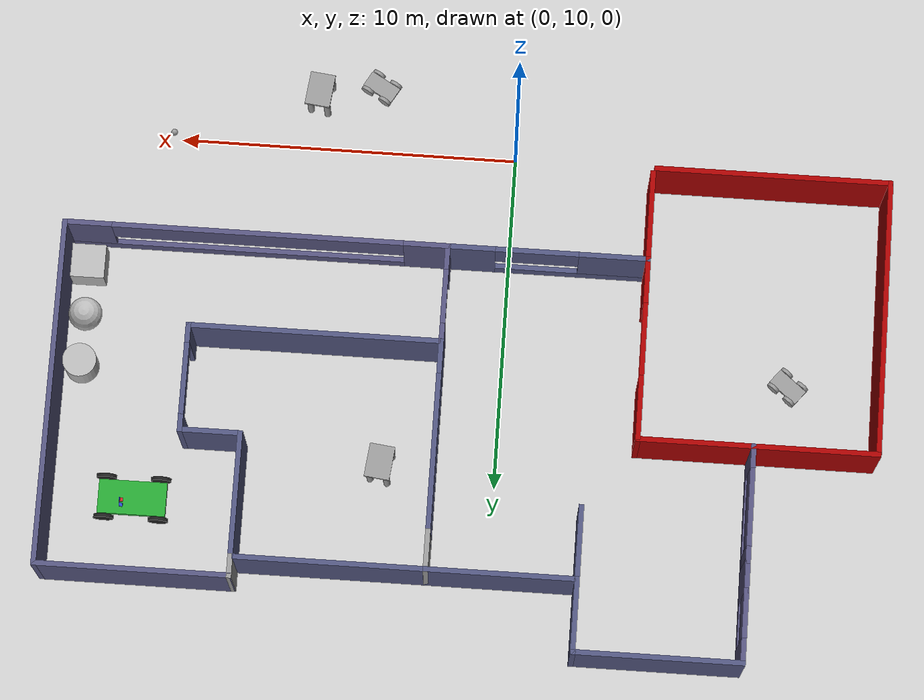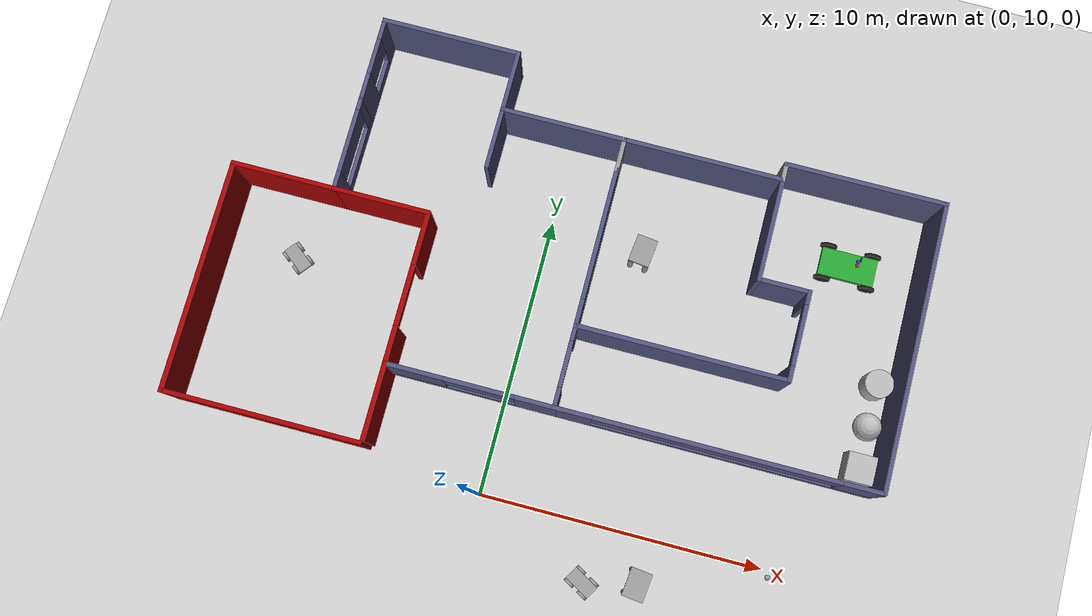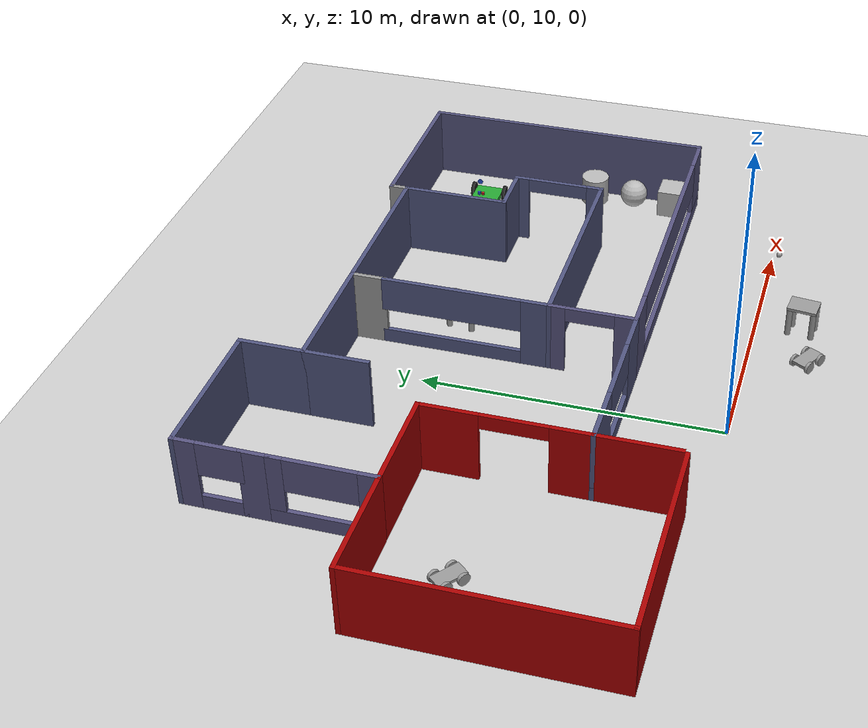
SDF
<sdf version="1.6">
 <world name="default">
  <plugin name="sample_factory_plugin" filename="libsample_factory_plugin.so"/>
  <light name="sun" type="directional">
   <pose>0 0 10 0 -0 0</pose>
   <diffuse>0.8 0.8 0.8 1</diffuse>
   <specular>0.2 0.2 0.2 1</specular>
   <attenuation>
    <range>1000</range>
    <constant>0.9</constant>
    <linear>0.01</linear>
    <quadratic>0.001</quadratic>
   </attenuation>
   <direction>-0.5 0.1 -0.9</direction>
  </light>
  <model name="ground_plane">
   <static>1</static>
   <link name="link">
    <collision name="collision">
     <geometry><plane><normal>0 0 1</normal><size>100 100</size></plane></geometry>
     <surface>
      <contact><collide_bitmask>65535</collide_bitmask></contact>
      <friction><ode><mu>100</mu><mu2>50</mu2></ode></friction>
     </surface>
    </collision>
    <visual name="visual">
     <cast_shadows>0</cast_shadows>
     <geometry><plane><normal>0 0 1</normal><size>100 100</size></plane></geometry>
     <material>
      <script><uri>file://media/materials/scripts/gazebo.material</uri><name>Gazebo/Grey</name></script>
     </material>
    </visual>
   </link>
  </model>
  <gravity>0 0 -9.8</gravity>
  <magnetic_field>6e-06 2.3e-05 -4.2e-05</magnetic_field>
  <atmosphere type="adiabatic"/>
  <physics name="default_physics" default="0" type="ode">
   <max_step_size>0.001</max_step_size>
   <real_time_factor>1</real_time_factor>
   <real_time_update_rate>1000</real_time_update_rate>
  </physics>
  <scene><ambient>0.4 0.4 0.4 1</ambient><background>0.7 0.7 0.7 1</background><shadows>1</shadows></scene>
  <spherical_coordinates>
   <surface_model>EARTH_WGS84</surface_model>
   <latitude_deg>0</latitude_deg>
   <longitude_deg>0</longitude_deg>
   <elevation>0</elevation>
   <heading_deg>0</heading_deg>
  </spherical_coordinates>
  <model name="Cart_clone">
   <link name="link_0">
    <pose>0 -0 0.048015 0 -0 0</pose>
    <inertial>
     <mass>1</mass>
     <inertia>
      <ixx>0.166667</ixx>
      <ixy>0</ixy>
      <ixz>0</ixz>
      <iyy>0.166667</iyy>
      <iyz>0</iyz>
      <izz>0.166667</izz>
     </inertia>
    </inertial>
    <visual name="visual">
     <geometry><box><size>0.5 1 0.1</size></box></geometry>
     <material>
      <lighting>1</lighting>
      <script><uri>file://media/materials/scripts/gazebo.material</uri><name>Gazebo/Grey</name></script>
      <shader type="pixel"><normal_map>__default__</normal_map></shader>
      <ambient>0.3 0.3 0.3 1</ambient>
      <diffuse>0.7 0.7 0.7 1</diffuse>
      <specular>0.01 0.01 0.01 1</specular>
      <emissive>0 0 0 1</emissive>
     </material>
    </visual>
    <collision name="collision">
     <geometry><box><size>0.5 1 0.1</size></box></geometry>
     <surface>
      <friction>
       <ode><mu>1</mu><mu2>1</mu2><fdir1>0 0 0</fdir1><slip1>0</slip1><slip2>0</slip2></ode>
       <torsional>
        <coefficient>1</coefficient>
        <patch_radius>0</patch_radius>
        <surface_radius>0</surface_radius>
        <use_patch_radius>1</use_patch_radius>
        <ode><slip>0</slip></ode>
       </torsional>
      </friction>
      <bounce><restitution_coefficient>0</restitution_coefficient><threshold>1e+06</threshold></bounce>
      <contact>
       <collide_without_contact>0</collide_without_contact>
       <collide_without_contact_bitmask>1</collide_without_contact_bitmask>
       <collide_bitmask>1</collide_bitmask>
       <ode>
        <soft_cfm>0</soft_cfm>
        <soft_erp>0.2</soft_erp>
        <kp>1e+13</kp>
        <kd>1</kd>
        <max_vel>0.01</max_vel>
        <min_depth>0</min_depth>
       </ode>
       <bullet>
        <split_impulse>1</split_impulse>
        <split_impulse_penetration_threshold>-0.01</split_impulse_penetration_threshold>
        <soft_cfm>0</soft_cfm>
        <soft_erp>0.2</soft_erp>
        <kp>1e+13</kp>
        <kd>1</kd>
       </bullet>
      </contact>
     </surface>
    </collision>
   </link>
   <link name="link_1_clone">
    <pose>-0.300001 -0.299981 -0.012004 1.5708 -9.6e-05 -1.5708</pose>
    <inertial>
     <mass>1</mass>
     <inertia><ixx>0.145833</ixx><ixy>0</ixy><ixz>0</ixz><iyy>0.145833</iyy><iyz>0</iyz><izz>0.125</izz></inertia>
    </inertial>
    <visual name="visual">
     <geometry><cylinder><radius>0.2</radius><length>0.1</length></cylinder></geometry>
     <material>
      <lighting>1</lighting>
      <script><uri>file://media/materials/scripts/gazebo.material</uri><name>Gazebo/Grey</name></script>
      <shader type="pixel"><normal_map>__default__</normal_map></shader>
      <ambient>0.3 0.3 0.3 1</ambient>
      <diffuse>0.7 0.7 0.7 1</diffuse>
      <specular>0.01 0.01 0.01 1</specular>
      <emissive>0 0 0 1</emissive>
     </material>
    </visual>
    <collision name="collision">
     <geometry><cylinder><radius>0.2</radius><length>0.1</length></cylinder></geometry>
     <surface>
      <friction>
       <ode><mu>1</mu><mu2>1</mu2><fdir1>0 0 0</fdir1><slip1>0</slip1><slip2>0</slip2></ode>
       <torsional>
        <coefficient>1</coefficient>
        <patch_radius>0</patch_radius>
        <surface_radius>0</surface_radius>
        <use_patch_radius>1</use_patch_radius>
        <ode><slip>0</slip></ode>
       </torsional>
      </friction>
      <bounce><restitution_coefficient>0</restitution_coefficient><threshold>1e+06</threshold></bounce>
      <contact>
       <collide_without_contact>0</collide_without_contact>
       <collide_without_contact_bitmask>1</collide_without_contact_bitmask>
       <collide_bitmask>1</collide_bitmask>
       <ode>
        <soft_cfm>0</soft_cfm>
        <soft_erp>0.2</soft_erp>
        <kp>1e+13</kp>
        <kd>1</kd>
        <max_vel>0.01</max_vel>
        <min_depth>0</min_depth>
       </ode>
       <bullet>
        <split_impulse>1</split_impulse>
        <split_impulse_penetration_threshold>-0.01</split_impulse_penetration_threshold>
        <soft_cfm>0</soft_cfm>
        <soft_erp>0.2</soft_erp>
        <kp>1e+13</kp>
        <kd>1</kd>
       </bullet>
      </contact>
     </surface>
    </collision>
   </link>
   <link name="link_1_clone_0">
    <pose>-0.300001 0.29998 -0.012004 1.5708 -9.6e-05 -1.5708</pose>
    <inertial>
     <mass>1</mass>
     <inertia><ixx>0.145833</ixx><ixy>0</ixy><ixz>0</ixz><iyy>0.145833</iyy><iyz>0</iyz><izz>0.125</izz></inertia>
    </inertial>
    <visual name="visual">
     <geometry><cylinder><radius>0.2</radius><length>0.1</length></cylinder></geometry>
     <material>
      <lighting>1</lighting>
      <script><uri>file://media/materials/scripts/gazebo.material</uri><name>Gazebo/Grey</name></script>
      <shader type="pixel"><normal_map>__default__</normal_map></shader>
      <ambient>0.3 0.3 0.3 1</ambient>
      <diffuse>0.7 0.7 0.7 1</diffuse>
      <specular>0.01 0.01 0.01 1</specular>
      <emissive>0 0 0 1</emissive>
     </material>
    </visual>
    <collision name="collision">
     <geometry><cylinder><radius>0.2</radius><length>0.1</length></cylinder></geometry>
     <surface>
      <friction>
       <ode><mu>1</mu><mu2>1</mu2><fdir1>0 0 0</fdir1><slip1>0</slip1><slip2>0</slip2></ode>
       <torsional>
        <coefficient>1</coefficient>
        <patch_radius>0</patch_radius>
        <surface_radius>0</surface_radius>
        <use_patch_radius>1</use_patch_radius>
        <ode><slip>0</slip></ode>
       </torsional>
      </friction>
      <bounce><restitution_coefficient>0</restitution_coefficient><threshold>1e+06</threshold></bounce>
      <contact>
       <collide_without_contact>0</collide_without_contact>
       <collide_without_contact_bitmask>1</collide_without_contact_bitmask>
       <collide_bitmask>1</collide_bitmask>
       <ode>
        <soft_cfm>0</soft_cfm>
        <soft_erp>0.2</soft_erp>
        <kp>1e+13</kp>
        <kd>1</kd>
        <max_vel>0.01</max_vel>
        <min_depth>0</min_depth>
       </ode>
       <bullet>
        <split_impulse>1</split_impulse>
        <split_impulse_penetration_threshold>-0.01</split_impulse_penetration_threshold>
        <soft_cfm>0</soft_cfm>
        <soft_erp>0.2</soft_erp>
        <kp>1e+13</kp>
        <kd>1</kd>
       </bullet>
      </contact>
     </surface>
    </collision>
   </link>
   <link name="link_1_clone_1">
    <pose>0.300002 0.29998 -0.012004 1.5708 -9.6e-05 -1.5708</pose>
    <inertial>
     <mass>1</mass>
     <inertia><ixx>0.145833</ixx><ixy>0</ixy><ixz>0</ixz><iyy>0.145833</iyy><iyz>0</iyz><izz>0.125</izz></inertia>
    </inertial>
    <visual name="visual">
     <geometry><cylinder><radius>0.2</radius><length>0.1</length></cylinder></geometry>
     <material>
      <lighting>1</lighting>
      <script><uri>file://media/materials/scripts/gazebo.material</uri><name>Gazebo/Grey</name></script>
      <shader type="pixel"><normal_map>__default__</normal_map></shader>
      <ambient>0.3 0.3 0.3 1</ambient>
      <diffuse>0.7 0.7 0.7 1</diffuse>
      <specular>0.01 0.01 0.01 1</specular>
      <emissive>0 0 0 1</emissive>
     </material>
    </visual>
    <collision name="collision">
     <geometry><cylinder><radius>0.2</radius><length>0.1</length></cylinder></geometry>
     <surface>
      <friction>
       <ode><mu>1</mu><mu2>1</mu2><fdir1>0 0 0</fdir1><slip1>0</slip1><slip2>0</slip2></ode>
       <torsional>
        <coefficient>1</coefficient>
        <patch_radius>0</patch_radius>
        <surface_radius>0</surface_radius>
        <use_patch_radius>1</use_patch_radius>
        <ode><slip>0</slip></ode>
       </torsional>
      </friction>
      <bounce><restitution_coefficient>0</restitution_coefficient><threshold>1e+06</threshold></bounce>
      <contact>
       <collide_without_contact>0</collide_without_contact>
       <collide_without_contact_bitmask>1</collide_without_contact_bitmask>
       <collide_bitmask>1</collide_bitmask>
       <ode>
        <soft_cfm>0</soft_cfm>
        <soft_erp>0.2</soft_erp>
        <kp>1e+13</kp>
        <kd>1</kd>
        <max_vel>0.01</max_vel>
        <min_depth>0</min_depth>
       </ode>
       <bullet>
        <split_impulse>1</split_impulse>
        <split_impulse_penetration_threshold>-0.01</split_impulse_penetration_threshold>
        <soft_cfm>0</soft_cfm>
        <soft_erp>0.2</soft_erp>
        <kp>1e+13</kp>
        <kd>1</kd>
       </bullet>
      </contact>
     </surface>
    </collision>
   </link>
   <link name="link_1_clone_1_clone">
    <pose>0.300002 -0.299981 -0.012004 1.5708 -9.6e-05 -1.5708</pose>
    <inertial>
     <mass>1</mass>
     <inertia><ixx>0.145833</ixx><ixy>0</ixy><ixz>0</ixz><iyy>0.145833</iyy><iyz>0</iyz><izz>0.125</izz></inertia>
    </inertial>
    <visual name="visual">
     <geometry><cylinder><radius>0.2</radius><length>0.1</length></cylinder></geometry>
     <material>
      <lighting>1</lighting>
      <script><uri>file://media/materials/scripts/gazebo.material</uri><name>Gazebo/Grey</name></script>
      <shader type="pixel"><normal_map>__default__</normal_map></shader>
      <ambient>0.3 0.3 0.3 1</ambient>
      <diffuse>0.7 0.7 0.7 1</diffuse>
      <specular>0.01 0.01 0.01 1</specular>
      <emissive>0 0 0 1</emissive>
     </material>
    </visual>
    <collision name="collision">
     <geometry><cylinder><radius>0.2</radius><length>0.1</length></cylinder></geometry>
     <surface>
      <friction>
       <ode><mu>1</mu><mu2>1</mu2><fdir1>0 0 0</fdir1><slip1>0</slip1><slip2>0</slip2></ode>
       <torsional>
        <coefficient>1</coefficient>
        <patch_radius>0</patch_radius>
        <surface_radius>0</surface_radius>
        <use_patch_radius>1</use_patch_radius>
        <ode><slip>0</slip></ode>
       </torsional>
      </friction>
      <bounce><restitution_coefficient>0</restitution_coefficient><threshold>1e+06</threshold></bounce>
      <contact>
       <collide_without_contact>0</collide_without_contact>
       <collide_without_contact_bitmask>1</collide_without_contact_bitmask>
       <collide_bitmask>1</collide_bitmask>
       <ode>
        <soft_cfm>0</soft_cfm>
        <soft_erp>0.2</soft_erp>
        <kp>1e+13</kp>
        <kd>1</kd>
        <max_vel>0.01</max_vel>
        <min_depth>0</min_depth>
       </ode>
       <bullet>
        <split_impulse>1</split_impulse>
        <split_impulse_penetration_threshold>-0.01</split_impulse_penetration_threshold>
        <soft_cfm>0</soft_cfm>
        <soft_erp>0.2</soft_erp>
        <kp>1e+13</kp>
        <kd>1</kd>
       </bullet>
      </contact>
     </surface>
    </collision>
   </link>
   <joint name="link_0_JOINT_0" type="revolute">
    <parent>link_0</parent>
    <child>link_1_clone</child>
    <axis>
     <xyz>0 0 1</xyz>
     <use_parent_model_frame>0</use_parent_model_frame>
     <limit>
      <lower>-1.79769e+308</lower>
      <upper>1.79769e+308</upper>
      <effort>-1</effort>
      <velocity>-1</velocity>
     </limit>
     <dynamics>
      <spring_reference>0</spring_reference>
      <spring_stiffness>0</spring_stiffness>
      <damping>0</damping>
     </dynamics>
    </axis>
    <physics>
     <ode><limit><cfm>0</cfm><erp>0.2</erp></limit><suspension><cfm>0</cfm><erp>0.2</erp></suspension></ode>
    </physics>
   </joint>
   <joint name="link_0_JOINT_1" type="revolute">
    <parent>link_0</parent>
    <child>link_1_clone_0</child>
    <axis>
     <xyz>0 0 1</xyz>
     <use_parent_model_frame>0</use_parent_model_frame>
     <limit>
      <lower>-1.79769e+308</lower>
      <upper>1.79769e+308</upper>
      <effort>-1</effort>
      <velocity>-1</velocity>
     </limit>
     <dynamics>
      <spring_reference>0</spring_reference>
      <spring_stiffness>0</spring_stiffness>
      <damping>0</damping>
     </dynamics>
    </axis>
    <physics>
     <ode><limit><cfm>0</cfm><erp>0.2</erp></limit><suspension><cfm>0</cfm><erp>0.2</erp></suspension></ode>
    </physics>
   </joint>
   <joint name="link_0_JOINT_2" type="revolute">
    <parent>link_0</parent>
    <child>link_1_clone_1</child>
    <axis>
     <xyz>0 0 1</xyz>
     <use_parent_model_frame>0</use_parent_model_frame>
     <limit>
      <lower>-1.79769e+308</lower>
      <upper>1.79769e+308</upper>
      <effort>-1</effort>
      <velocity>-1</velocity>
     </limit>
     <dynamics>
      <spring_reference>0</spring_reference>
      <spring_stiffness>0</spring_stiffness>
      <damping>0</damping>
     </dynamics>
    </axis>
    <physics>
     <ode><limit><cfm>0</cfm><erp>0.2</erp></limit><suspension><cfm>0</cfm><erp>0.2</erp></suspension></ode>
    </physics>
   </joint>
   <joint name="link_0_JOINT_5" type="revolute">
    <parent>link_0</parent>
    <child>link_1_clone_1_clone</child>
    <axis>
     <xyz>0 0 1</xyz>
     <use_parent_model_frame>0</use_parent_model_frame>
     <limit>
      <lower>-1.79769e+308</lower>
      <upper>1.79769e+308</upper>
      <effort>-1</effort>
      <velocity>-1</velocity>
     </limit>
     <dynamics>
      <spring_reference>0</spring_reference>
      <spring_stiffness>0</spring_stiffness>
      <damping>0</damping>
     </dynamics>
    </axis>
    <physics>
     <ode><limit><cfm>0</cfm><erp>0.2</erp></limit><suspension><cfm>0</cfm><erp>0.2</erp></suspension></ode>
    </physics>
   </joint>
   <static>0</static>
   <pose>4.15523 8.02364 0.211998 -1.2e-05 -0 1.04534</pose>
  </model>
  <model name="Walker">
   <link name="link_2">
    <pose>0.008 0.008 0.440001 0 -0 0</pose>
    <inertial>
     <mass>1</mass>
     <inertia>
      <ixx>0.166667</ixx>
      <ixy>0</ixy>
      <ixz>0</ixz>
      <iyy>0.166667</iyy>
      <iyz>0</iyz>
      <izz>0.166667</izz>
     </inertia>
    </inertial>
    <visual name="visual">
     <geometry><box><size>0.75 1 0.1</size></box></geometry>
     <material>
      <lighting>1</lighting>
      <script><uri>file://media/materials/scripts/gazebo.material</uri><name>Gazebo/Grey</name></script>
      <shader type="pixel"><normal_map>__default__</normal_map></shader>
      <ambient>0.3 0.3 0.3 1</ambient>
      <diffuse>0.7 0.7 0.7 1</diffuse>
      <specular>0.01 0.01 0.01 1</specular>
      <emissive>0 0 0 1</emissive>
     </material>
    </visual>
    <collision name="collision">
     <geometry><box><size>0.75 1 0.1</size></box></geometry>
     <surface>
      <friction>
       <ode><mu>1</mu><mu2>1</mu2><fdir1>0 0 0</fdir1><slip1>0</slip1><slip2>0</slip2></ode>
       <torsional>
        <coefficient>1</coefficient>
        <patch_radius>0</patch_radius>
        <surface_radius>0</surface_radius>
        <use_patch_radius>1</use_patch_radius>
        <ode><slip>0</slip></ode>
       </torsional>
      </friction>
      <bounce><restitution_coefficient>0</restitution_coefficient><threshold>1e+06</threshold></bounce>
      <contact>
       <collide_without_contact>0</collide_without_contact>
       <collide_without_contact_bitmask>1</collide_without_contact_bitmask>
       <collide_bitmask>1</collide_bitmask>
       <ode>
        <soft_cfm>0</soft_cfm>
        <soft_erp>0.2</soft_erp>
        <kp>1e+13</kp>
        <kd>1</kd>
        <max_vel>0.01</max_vel>
        <min_depth>0</min_depth>
       </ode>
       <bullet>
        <split_impulse>1</split_impulse>
        <split_impulse_penetration_threshold>-0.01</split_impulse_penetration_threshold>
        <soft_cfm>0</soft_cfm>
        <soft_erp>0.2</soft_erp>
        <kp>1e+13</kp>
        <kd>1</kd>
       </bullet>
      </contact>
     </surface>
    </collision>
   </link>
   <link name="link_3">
    <pose>0.243 0.368 -0.109999 0 -0 0</pose>
    <inertial>
     <mass>1</mass>
     <inertia><ixx>0.145833</ixx><ixy>0</ixy><ixz>0</ixz><iyy>0.145833</iyy><iyz>0</iyz><izz>0.125</izz></inertia>
    </inertial>
    <visual name="visual">
     <geometry><cylinder><radius>0.1</radius><length>1</length></cylinder></geometry>
     <material>
      <lighting>1</lighting>
      <script><uri>file://media/materials/scripts/gazebo.material</uri><name>Gazebo/Grey</name></script>
      <shader type="pixel"><normal_map>__default__</normal_map></shader>
      <ambient>0.3 0.3 0.3 1</ambient>
      <diffuse>0.7 0.7 0.7 1</diffuse>
      <specular>0.01 0.01 0.01 1</specular>
      <emissive>0 0 0 1</emissive>
     </material>
    </visual>
    <collision name="collision">
     <geometry><cylinder><radius>0.1</radius><length>1</length></cylinder></geometry>
     <surface>
      <friction>
       <ode><mu>1</mu><mu2>1</mu2><fdir1>0 0 0</fdir1><slip1>0</slip1><slip2>0</slip2></ode>
       <torsional>
        <coefficient>1</coefficient>
        <patch_radius>0</patch_radius>
        <surface_radius>0</surface_radius>
        <use_patch_radius>1</use_patch_radius>
        <ode><slip>0</slip></ode>
       </torsional>
      </friction>
      <bounce><restitution_coefficient>0</restitution_coefficient><threshold>1e+06</threshold></bounce>
      <contact>
       <collide_without_contact>0</collide_without_contact>
       <collide_without_contact_bitmask>1</collide_without_contact_bitmask>
       <collide_bitmask>1</collide_bitmask>
       <ode>
        <soft_cfm>0</soft_cfm>
        <soft_erp>0.2</soft_erp>
        <kp>1e+13</kp>
        <kd>1</kd>
        <max_vel>0.01</max_vel>
        <min_depth>0</min_depth>
       </ode>
       <bullet>
        <split_impulse>1</split_impulse>
        <split_impulse_penetration_threshold>-0.01</split_impulse_penetration_threshold>
        <soft_cfm>0</soft_cfm>
        <soft_erp>0.2</soft_erp>
        <kp>1e+13</kp>
        <kd>1</kd>
       </bullet>
      </contact>
     </surface>
    </collision>
   </link>
   <link name="link_3_clone">
    <pose>0.283 -0.392001 -0.109999 0 -0 0</pose>
    <inertial>
     <mass>1</mass>
     <inertia><ixx>0.145833</ixx><ixy>0</ixy><ixz>0</ixz><iyy>0.145833</iyy><iyz>0</iyz><izz>0.125</izz></inertia>
    </inertial>
    <visual name="visual">
     <geometry><cylinder><radius>0.1</radius><length>1</length></cylinder></geometry>
     <material>
      <lighting>1</lighting>
      <script><uri>file://media/materials/scripts/gazebo.material</uri><name>Gazebo/Grey</name></script>
      <shader type="pixel"><normal_map>__default__</normal_map></shader>
      <ambient>0.3 0.3 0.3 1</ambient>
      <diffuse>0.7 0.7 0.7 1</diffuse>
      <specular>0.01 0.01 0.01 1</specular>
      <emissive>0 0 0 1</emissive>
     </material>
    </visual>
    <collision name="collision">
     <geometry><cylinder><radius>0.1</radius><length>1</length></cylinder></geometry>
     <surface>
      <friction>
       <ode><mu>1</mu><mu2>1</mu2><fdir1>0 0 0</fdir1><slip1>0</slip1><slip2>0</slip2></ode>
       <torsional>
        <coefficient>1</coefficient>
        <patch_radius>0</patch_radius>
        <surface_radius>0</surface_radius>
        <use_patch_radius>1</use_patch_radius>
        <ode><slip>0</slip></ode>
       </torsional>
      </friction>
      <bounce><restitution_coefficient>0</restitution_coefficient><threshold>1e+06</threshold></bounce>
      <contact>
       <collide_without_contact>0</collide_without_contact>
       <collide_without_contact_bitmask>1</collide_without_contact_bitmask>
       <collide_bitmask>1</collide_bitmask>
       <ode>
        <soft_cfm>0</soft_cfm>
        <soft_erp>0.2</soft_erp>
        <kp>1e+13</kp>
        <kd>1</kd>
        <max_vel>0.01</max_vel>
        <min_depth>0</min_depth>
       </ode>
       <bullet>
        <split_impulse>1</split_impulse>
        <split_impulse_penetration_threshold>-0.01</split_impulse_penetration_threshold>
        <soft_cfm>0</soft_cfm>
        <soft_erp>0.2</soft_erp>
        <kp>1e+13</kp>
        <kd>1</kd>
       </bullet>
      </contact>
     </surface>
    </collision>
   </link>
   <link name="link_3_clone_0">
    <pose>-0.267 0.407999 -0.109999 0 -0 0</pose>
    <inertial>
     <mass>1</mass>
     <inertia><ixx>0.145833</ixx><ixy>0</ixy><ixz>0</ixz><iyy>0.145833</iyy><iyz>0</iyz><izz>0.125</izz></inertia>
    </inertial>
    <visual name="visual">
     <geometry><cylinder><radius>0.1</radius><length>1</length></cylinder></geometry>
     <material>
      <lighting>1</lighting>
      <script><uri>file://media/materials/scripts/gazebo.material</uri><name>Gazebo/Grey</name></script>
      <shader type="pixel"><normal_map>__default__</normal_map></shader>
      <ambient>0.3 0.3 0.3 1</ambient>
      <diffuse>0.7 0.7 0.7 1</diffuse>
      <specular>0.01 0.01 0.01 1</specular>
      <emissive>0 0 0 1</emissive>
     </material>
    </visual>
    <collision name="collision">
     <geometry><cylinder><radius>0.1</radius><length>1</length></cylinder></geometry>
     <surface>
      <friction>
       <ode><mu>1</mu><mu2>1</mu2><fdir1>0 0 0</fdir1><slip1>0</slip1><slip2>0</slip2></ode>
       <torsional>
        <coefficient>1</coefficient>
        <patch_radius>0</patch_radius>
        <surface_radius>0</surface_radius>
        <use_patch_radius>1</use_patch_radius>
        <ode><slip>0</slip></ode>
       </torsional>
      </friction>
      <bounce><restitution_coefficient>0</restitution_coefficient><threshold>1e+06</threshold></bounce>
      <contact>
       <collide_without_contact>0</collide_without_contact>
       <collide_without_contact_bitmask>1</collide_without_contact_bitmask>
       <collide_bitmask>1</collide_bitmask>
       <ode>
        <soft_cfm>0</soft_cfm>
        <soft_erp>0.2</soft_erp>
        <kp>1e+13</kp>
        <kd>1</kd>
        <max_vel>0.01</max_vel>
        <min_depth>0</min_depth>
       </ode>
       <bullet>
        <split_impulse>1</split_impulse>
        <split_impulse_penetration_threshold>-0.01</split_impulse_penetration_threshold>
        <soft_cfm>0</soft_cfm>
        <soft_erp>0.2</soft_erp>
        <kp>1e+13</kp>
        <kd>1</kd>
       </bullet>
      </contact>
     </surface>
    </collision>
   </link>
   <link name="link_3_clone_1">
    <pose>-0.267 -0.392001 -0.109999 0 -0 0</pose>
    <inertial>
     <mass>1</mass>
     <inertia><ixx>0.145833</ixx><ixy>0</ixy><ixz>0</ixz><iyy>0.145833</iyy><iyz>0</iyz><izz>0.125</izz></inertia>
    </inertial>
    <visual name="visual">
     <geometry><cylinder><radius>0.1</radius><length>1</length></cylinder></geometry>
     <material>
      <lighting>1</lighting>
      <script><uri>file://media/materials/scripts/gazebo.material</uri><name>Gazebo/Grey</name></script>
      <shader type="pixel"><normal_map>__default__</normal_map></shader>
      <ambient>0.3 0.3 0.3 1</ambient>
      <diffuse>0.7 0.7 0.7 1</diffuse>
      <specular>0.01 0.01 0.01 1</specular>
      <emissive>0 0 0 1</emissive>
     </material>
    </visual>
    <collision name="collision">
     <geometry><cylinder><radius>0.1</radius><length>1</length></cylinder></geometry>
     <surface>
      <friction>
       <ode><mu>1</mu><mu2>1</mu2><fdir1>0 0 0</fdir1><slip1>0</slip1><slip2>0</slip2></ode>
       <torsional>
        <coefficient>1</coefficient>
        <patch_radius>0</patch_radius>
        <surface_radius>0</surface_radius>
        <use_patch_radius>1</use_patch_radius>
        <ode><slip>0</slip></ode>
       </torsional>
      </friction>
      <bounce><restitution_coefficient>0</restitution_coefficient><threshold>1e+06</threshold></bounce>
      <contact>
       <collide_without_contact>0</collide_without_contact>
       <collide_without_contact_bitmask>1</collide_without_contact_bitmask>
       <collide_bitmask>1</collide_bitmask>
       <ode>
        <soft_cfm>0</soft_cfm>
        <soft_erp>0.2</soft_erp>
        <kp>1e+13</kp>
        <kd>1</kd>
        <max_vel>0.01</max_vel>
        <min_depth>0</min_depth>
       </ode>
       <bullet>
        <split_impulse>1</split_impulse>
        <split_impulse_penetration_threshold>-0.01</split_impulse_penetration_threshold>
        <soft_cfm>0</soft_cfm>
        <soft_erp>0.2</soft_erp>
        <kp>1e+13</kp>
        <kd>1</kd>
       </bullet>
      </contact>
     </surface>
    </collision>
   </link>
   <joint name="link_2_JOINT_6" type="revolute">
    <parent>link_2</parent>
    <child>link_3</child>
    <axis>
     <xyz>1 0 0</xyz>
     <use_parent_model_frame>0</use_parent_model_frame>
     <limit>
      <lower>-1.79769e+308</lower>
      <upper>1.79769e+308</upper>
      <effort>-1</effort>
      <velocity>-1</velocity>
     </limit>
     <dynamics>
      <spring_reference>0</spring_reference>
      <spring_stiffness>0</spring_stiffness>
      <damping>0</damping>
     </dynamics>
    </axis>
    <physics>
     <ode><limit><cfm>0</cfm><erp>0.2</erp></limit><suspension><cfm>0</cfm><erp>0.2</erp></suspension></ode>
    </physics>
   </joint>
   <joint name="link_2_JOINT_7" type="revolute">
    <parent>link_2</parent>
    <child>link_3_clone_0</child>
    <axis>
     <xyz>1 0 0</xyz>
     <use_parent_model_frame>0</use_parent_model_frame>
     <limit>
      <lower>-1.79769e+308</lower>
      <upper>1.79769e+308</upper>
      <effort>-1</effort>
      <velocity>-1</velocity>
     </limit>
     <dynamics>
      <spring_reference>0</spring_reference>
      <spring_stiffness>0</spring_stiffness>
      <damping>0</damping>
     </dynamics>
    </axis>
    <physics>
     <ode><limit><cfm>0</cfm><erp>0.2</erp></limit><suspension><cfm>0</cfm><erp>0.2</erp></suspension></ode>
    </physics>
   </joint>
   <joint name="link_2_JOINT_8" type="revolute">
    <parent>link_2</parent>
    <child>link_3_clone</child>
    <axis>
     <xyz>1 0 0</xyz>
     <use_parent_model_frame>0</use_parent_model_frame>
     <limit>
      <lower>-1.79769e+308</lower>
      <upper>1.79769e+308</upper>
      <effort>-1</effort>
      <velocity>-1</velocity>
     </limit>
     <dynamics>
      <spring_reference>0</spring_reference>
      <spring_stiffness>0</spring_stiffness>
      <damping>0</damping>
     </dynamics>
    </axis>
    <physics>
     <ode><limit><cfm>0</cfm><erp>0.2</erp></limit><suspension><cfm>0</cfm><erp>0.2</erp></suspension></ode>
    </physics>
   </joint>
   <joint name="link_2_JOINT_9" type="revolute">
    <parent>link_2</parent>
    <child>link_3_clone_1</child>
    <axis>
     <xyz>1 0 0</xyz>
     <use_parent_model_frame>0</use_parent_model_frame>
     <limit>
      <lower>-1.79769e+308</lower>
      <upper>1.79769e+308</upper>
      <effort>-1</effort>
      <velocity>-1</velocity>
     </limit>
     <dynamics>
      <spring_reference>0</spring_reference>
      <spring_stiffness>0</spring_stiffness>
      <damping>0</damping>
     </dynamics>
    </axis>
    <physics>
     <ode><limit><cfm>0</cfm><erp>0.2</erp></limit><suspension><cfm>0</cfm><erp>0.2</erp></suspension></ode>
    </physics>
   </joint>
   <static>0</static>
   <pose>5.94083 8.44628 0.609999 -0 -1e-06 -0.115844</pose>
  </model>
  <model name="Apartment_02">
   <pose>0.99714 17.8132 0 0 -0 0</pose>
   <link name="Wall_141">
    <collision name="Wall_141_Collision">
     <geometry><box><size>7.5 0.15 2.5</size></box></geometry>
     <pose>0 0 1.25 0 -0 0</pose>
    </collision>
    <visual name="Wall_141_Visual">
     <pose>0 0 1.25 0 -0 0</pose>
     <geometry><box><size>7.5 0.15 2.5</size></box></geometry>
     <material>
      <script><uri>file://media/materials/scripts/gazebo.material</uri><name>Gazebo/Grey</name></script>
      <ambient>0.317647 0.333333 0.498039 1</ambient>
     </material>
     <meta><layer>0</layer></meta>
    </visual>
    <pose>4.47349 -1.6 0 0 -0 3.14159</pose>
   </link>
   <link name="Wall_142">
    <pose>0.798496 -3.025 0 0 0 -1.5708</pose>
    <visual name="Wall_142_Visual_0">
     <pose>-1.19377 0 1.25 0 -0 0</pose>
     <geometry><box><size>0.612455 0.15 2.5</size></box></geometry>
     <material>
      <script><uri>file://media/materials/scripts/gazebo.material</uri><name>Gazebo/Grey</name></script>
      <ambient>0.341176 0.329412 0.498039 1</ambient>
     </material>
     <meta><layer>0</layer></meta>
    </visual>
    <collision name="Wall_142_Collision_0">
     <geometry><box><size>0.612455 0.15 2.5</size></box></geometry>
     <pose>-1.19377 0 1.25 0 -0 0</pose>
    </collision>
    <visual name="Wall_142_Visual_1">
     <pose>1.11465 0 1.25 0 -0 0</pose>
     <geometry><box><size>0.770704 0.15 2.5</size></box></geometry>
     <material>
      <script><uri>file://media/materials/scripts/gazebo.material</uri><name>Gazebo/Grey</name></script>
      <ambient>0.341176 0.329412 0.498039 1</ambient>
     </material>
     <meta><layer>0</layer></meta>
    </visual>
    <collision name="Wall_142_Collision_1">
     <geometry><box><size>0.770704 0.15 2.5</size></box></geometry>
     <pose>1.11465 0 1.25 0 -0 0</pose>
    </collision>
    <visual name="Wall_142_Visual_2">
     <pose>-0.079125 0 2.25 0 -0 0</pose>
     <geometry><box><size>1.61684 0.15 0.5</size></box></geometry>
     <material>
      <script><uri>file://media/materials/scripts/gazebo.material</uri><name>Gazebo/Grey</name></script>
      <ambient>0.341176 0.329412 0.498039 1</ambient>
     </material>
     <meta><layer>0</layer></meta>
    </visual>
    <collision name="Wall_142_Collision_2">
     <geometry><box><size>1.61684 0.15 0.5</size></box></geometry>
     <pose>-0.079125 0 2.25 0 -0 0</pose>
    </collision>
   </link>
   <link name="Wall_143">
    <pose>-2.1265 -4.45 0 0 -0 3.14159</pose>
    <visual name="Wall_143_Visual_0">
     <pose>-2.26881 0 1.25 0 -0 0</pose>
     <geometry><box><size>1.46237 0.15 2.5</size></box></geometry>
     <material>
      <script><uri>file://media/materials/scripts/gazebo.material</uri><name>Gazebo/Grey</name></script>
      <ambient>0.317647 0.333333 0.498039 1</ambient>
     </material>
     <meta><layer>0</layer></meta>
    </visual>
    <collision name="Wall_143_Collision_0">
     <geometry><box><size>1.46237 0.15 2.5</size></box></geometry>
     <pose>-2.26881 0 1.25 0 -0 0</pose>
    </collision>
    <visual name="Wall_143_Visual_1">
     <pose>0.731186 0 0.25 0 -0 0</pose>
     <geometry><box><size>4.53763 0.15 0.5</size></box></geometry>
     <material>
      <script><uri>file://media/materials/scripts/gazebo.material</uri><name>Gazebo/Grey</name></script>
      <ambient>0.317647 0.333333 0.498039 1</ambient>
     </material>
     <meta><layer>0</layer></meta>
    </visual>
    <collision name="Wall_143_Collision_1">
     <geometry><box><size>4.53763 0.15 0.5</size></box></geometry>
     <pose>0.731186 0 0.25 0 -0 0</pose>
    </collision>
    <visual name="Wall_143_Visual_2">
     <pose>1.95114 0 1.5 0 -0 0</pose>
     <geometry><box><size>2.09773 0.15 2</size></box></geometry>
     <material>
      <script><uri>file://media/materials/scripts/gazebo.material</uri><name>Gazebo/Grey</name></script>
      <ambient>0.317647 0.333333 0.498039 1</ambient>
     </material>
     <meta><layer>0</layer></meta>
    </visual>
    <collision name="Wall_143_Collision_2">
     <geometry><box><size>2.09773 0.15 2</size></box></geometry>
     <pose>1.95114 0 1.5 0 -0 0</pose>
    </collision>
    <visual name="Wall_143_Visual_3">
     <pose>-0.317677 0 1.9 0 -0 0</pose>
     <geometry><box><size>2.4399 0.15 1.2</size></box></geometry>
     <material>
      <script><uri>file://media/materials/scripts/gazebo.material</uri><name>Gazebo/Grey</name></script>
      <ambient>0.317647 0.333333 0.498039 1</ambient>
     </material>
     <meta><layer>0</layer></meta>
    </visual>
    <collision name="Wall_143_Collision_3">
     <geometry><box><size>2.4399 0.15 1.2</size></box></geometry>
     <pose>-0.317677 0 1.9 0 -0 0</pose>
    </collision>
   </link>
   <link name="Wall_144">
    <pose>-5.0515 -1.775 0 0 -0 1.5708</pose>
    <visual name="Wall_144_Visual_0">
     <pose>-2.05414 0 1.25 0 -0 0</pose>
     <geometry><box><size>1.39172 0.15 2.5</size></box></geometry>
     <material>
      <script><uri>file://media/materials/scripts/gazebo.material</uri><name>Gazebo/Grey</name></script>
      <ambient>0.666667 0 0 1</ambient>
     </material>
     <meta><layer>0</layer></meta>
    </visual>
    <collision name="Wall_144_Collision_0">
     <geometry><box><size>1.39172 0.15 2.5</size></box></geometry>
     <pose>-2.05414 0 1.25 0 -0 0</pose>
    </collision>
    <visual name="Wall_144_Visual_1">
     <pose>1.76942 0 1.25 0 -0 0</pose>
     <geometry><box><size>1.96116 0.15 2.5</size></box></geometry>
     <material>
      <script><uri>file://media/materials/scripts/gazebo.material</uri><name>Gazebo/Grey</name></script>
      <ambient>0.666667 0 0 1</ambient>
     </material>
     <meta><layer>0</layer></meta>
    </visual>
    <collision name="Wall_144_Collision_1">
     <geometry><box><size>1.96116 0.15 2.5</size></box></geometry>
     <pose>1.76942 0 1.25 0 -0 0</pose>
    </collision>
    <visual name="Wall_144_Visual_2">
     <pose>-0.284718 0 2.25 0 -0 0</pose>
     <geometry><box><size>2.14712 0.15 0.5</size></box></geometry>
     <material>
      <script><uri>file://media/materials/scripts/gazebo.material</uri><name>Gazebo/Grey</name></script>
      <ambient>0.666667 0 0 1</ambient>
     </material>
     <meta><layer>0</layer></meta>
    </visual>
    <collision name="Wall_144_Collision_2">
     <geometry><box><size>2.14712 0.15 0.5</size></box></geometry>
     <pose>-0.284718 0 2.25 0 -0 0</pose>
    </collision>
   </link>
   <link name="Wall_145">
    <collision name="Wall_145_Collision">
     <geometry><box><size>3.5 0.15 2.5</size></box></geometry>
     <pose>0 0 1.25 0 -0 0</pose>
    </collision>
    <visual name="Wall_145_Visual">
     <pose>0 0 1.25 0 -0 0</pose>
     <geometry><box><size>3.5 0.15 2.5</size></box></geometry>
     <material>
      <script><uri>file://media/materials/scripts/gazebo.material</uri><name>Gazebo/Grey</name></script>
      <ambient>0.666667 0 0 1</ambient>
     </material>
     <meta><layer>0</layer></meta>
    </visual>
    <pose>-6.72651 0.9 0 0 -0 3.14159</pose>
   </link>
   <link name="Wall_146">
    <pose>-8.4015 2.575 0 0 -0 1.5708</pose>
    <visual name="Wall_146_Visual_0">
     <pose>-1.3991 0 1.25 0 -0 0</pose>
     <geometry><box><size>0.701801 0.15 2.5</size></box></geometry>
     <material>
      <script><uri>file://media/materials/scripts/gazebo.material</uri><name>Gazebo/Grey</name></script>
      <ambient>0.341176 0.329412 0.498039 1</ambient>
     </material>
     <meta><layer>0</layer></meta>
    </visual>
    <collision name="Wall_146_Collision_0">
     <geometry><box><size>0.701801 0.15 2.5</size></box></geometry>
     <pose>-1.3991 0 1.25 0 -0 0</pose>
    </collision>
    <visual name="Wall_146_Visual_1">
     <pose>0.3509 0 0.25 0 -0 0</pose>
     <geometry><box><size>2.7982 0.15 0.5</size></box></geometry>
     <material>
      <script><uri>file://media/materials/scripts/gazebo.material</uri><name>Gazebo/Grey</name></script>
      <ambient>0.341176 0.329412 0.498039 1</ambient>
     </material>
     <meta><layer>0</layer></meta>
    </visual>
    <collision name="Wall_146_Collision_1">
     <geometry><box><size>2.7982 0.15 0.5</size></box></geometry>
     <pose>0.3509 0 0.25 0 -0 0</pose>
    </collision>
    <visual name="Wall_146_Visual_2">
     <pose>1.4915 0 1.5 0 -0 0</pose>
     <geometry><box><size>0.516999 0.15 2</size></box></geometry>
     <material>
      <script><uri>file://media/materials/scripts/gazebo.material</uri><name>Gazebo/Grey</name></script>
      <ambient>0.341176 0.329412 0.498039 1</ambient>
     </material>
     <meta><layer>0</layer></meta>
    </visual>
    <collision name="Wall_146_Collision_2">
     <geometry><box><size>0.516999 0.15 2</size></box></geometry>
     <pose>1.4915 0 1.5 0 -0 0</pose>
    </collision>
    <visual name="Wall_146_Visual_3">
     <pose>0.092401 0 1.9 0 -0 0</pose>
     <geometry><box><size>2.2812 0.15 1.2</size></box></geometry>
     <material>
      <script><uri>file://media/materials/scripts/gazebo.material</uri><name>Gazebo/Grey</name></script>
      <ambient>0.341176 0.329412 0.498039 1</ambient>
     </material>
     <meta><layer>0</layer></meta>
    </visual>
    <collision name="Wall_146_Collision_3">
     <geometry><box><size>2.2812 0.15 1.2</size></box></geometry>
     <pose>0.092401 0 1.9 0 -0 0</pose>
    </collision>
   </link>
   <link name="Wall_147">
    <collision name="Wall_147_Collision">
     <geometry><box><size>1 0.15 2.5</size></box></geometry>
     <pose>0 0 1.25 0 -0 0</pose>
    </collision>
    <visual name="Wall_147_Visual">
     <pose>0 0 1.25 0 -0 0</pose>
     <geometry><box><size>1 0.15 2.5</size></box></geometry>
     <material>
      <script><uri>file://media/materials/scripts/gazebo.material</uri><name>Gazebo/Grey</name></script>
      <ambient>0.341176 0.329412 0.498039 1</ambient>
     </material>
     <meta><layer>0</layer></meta>
    </visual>
    <pose>-8.4015 4.675 0 0 -0 1.5708</pose>
   </link>
   <link name="Wall_151">
    <pose>0.798496 1.2 0 0 -0 1.5708</pose>
    <visual name="Wall_151_Visual_0">
     <pose>-2.36504 0 1.25 0 -0 0</pose>
     <geometry><box><size>1.01992 0.15 2.5</size></box></geometry>
     <material>
      <script><uri>file://media/materials/scripts/gazebo.material</uri><name>Gazebo/Grey</name></script>
      <ambient>0.317647 0.333333 0.498039 1</ambient>
     </material>
     <meta><layer>0</layer></meta>
    </visual>
    <collision name="Wall_151_Collision_0">
     <geometry><box><size>1.01992 0.15 2.5</size></box></geometry>
     <pose>-2.36504 0 1.25 0 -0 0</pose>
    </collision>
    <visual name="Wall_151_Visual_1">
     <pose>0.509958 0 0.25 0 -0 0</pose>
     <geometry><box><size>4.73008 0.15 0.5</size></box></geometry>
     <material>
      <script><uri>file://media/materials/scripts/gazebo.material</uri><name>Gazebo/Grey</name></script>
      <ambient>0.317647 0.333333 0.498039 1</ambient>
     </material>
     <meta><layer>0</layer></meta>
    </visual>
    <collision name="Wall_151_Collision_1">
     <geometry><box><size>4.73008 0.15 0.5</size></box></geometry>
     <pose>0.509958 0 0.25 0 -0 0</pose>
    </collision>
    <visual name="Wall_151_Visual_2">
     <pose>0.509958 0 1.9 0 -0 0</pose>
     <geometry><box><size>4.73008 0.15 1.2</size></box></geometry>
     <material>
      <script><uri>file://media/materials/scripts/gazebo.material</uri><name>Gazebo/Grey</name></script>
      <ambient>0.317647 0.333333 0.498039 1</ambient>
     </material>
     <meta><layer>0</layer></meta>
    </visual>
    <collision name="Wall_151_Collision_2">
     <geometry><box><size>4.73008 0.15 1.2</size></box></geometry>
     <pose>0.509958 0 1.9 0 -0 0</pose>
    </collision>
   </link>
   <link name="Wall_155">
    <pose>6.34849 -4.45 0 0 -0 0</pose>
    <visual name="Wall_155_Visual_0">
     <pose>-4.93549 0 1.25 0 -0 0</pose>
     <geometry><box><size>1.37903 0.15 2.5</size></box></geometry>
     <material>
      <script><uri>file://media/materials/scripts/gazebo.material</uri><name>Gazebo/Grey</name></script>
      <ambient>0.341176 0.329412 0.498039 1</ambient>
     </material>
     <meta><layer>0</layer></meta>
    </visual>
    <collision name="Wall_155_Collision_0">
     <geometry><box><size>1.37903 0.15 2.5</size></box></geometry>
     <pose>-4.93549 0 1.25 0 -0 0</pose>
    </collision>
    <visual name="Wall_155_Visual_1">
     <pose>0.689514 0 0.25 0 -0 0</pose>
     <geometry><box><size>9.87097 0.15 0.5</size></box></geometry>
     <material>
      <script><uri>file://media/materials/scripts/gazebo.material</uri><name>Gazebo/Grey</name></script>
      <ambient>0.341176 0.329412 0.498039 1</ambient>
     </material>
     <meta><layer>0</layer></meta>
    </visual>
    <collision name="Wall_155_Collision_1">
     <geometry><box><size>9.87097 0.15 0.5</size></box></geometry>
     <pose>0.689514 0 0.25 0 -0 0</pose>
    </collision>
    <visual name="Wall_155_Visual_2">
     <pose>4.95121 0 1.5 0 -0 0</pose>
     <geometry><box><size>1.34757 0.15 2</size></box></geometry>
     <material>
      <script><uri>file://media/materials/scripts/gazebo.material</uri><name>Gazebo/Grey</name></script>
      <ambient>0.341176 0.329412 0.498039 1</ambient>
     </material>
     <meta><layer>0</layer></meta>
    </visual>
    <collision name="Wall_155_Collision_2">
     <geometry><box><size>1.34757 0.15 2</size></box></geometry>
     <pose>4.95121 0 1.5 0 -0 0</pose>
    </collision>
    <visual name="Wall_155_Visual_3">
     <pose>0.015727 0 1.9 0 -0 0</pose>
     <geometry><box><size>8.5234 0.15 1.2</size></box></geometry>
     <material>
      <script><uri>file://media/materials/scripts/gazebo.material</uri><name>Gazebo/Grey</name></script>
      <ambient>0.341176 0.329412 0.498039 1</ambient>
     </material>
     <meta><layer>0</layer></meta>
    </visual>
    <collision name="Wall_155_Collision_3">
     <geometry><box><size>8.5234 0.15 1.2</size></box></geometry>
     <pose>0.015727 0 1.9 0 -0 0</pose>
    </collision>
   </link>
   <link name="Wall_157">
    <collision name="Wall_157_Collision">
     <geometry><box><size>5.75 0.15 2.5</size></box></geometry>
     <pose>0 0 1.25 0 -0 0</pose>
    </collision>
    <visual name="Wall_157_Visual">
     <pose>0 0 1.25 0 -0 0</pose>
     <geometry><box><size>5.75 0.15 2.5</size></box></geometry>
     <material>
      <script><uri>file://media/materials/scripts/gazebo.material</uri><name>Gazebo/Grey</name></script>
      <ambient>0.333333 0.333333 0.498039 1</ambient>
     </material>
     <meta><layer>0</layer></meta>
    </visual>
    <pose>9.2015 5.65865 0 0 -0 3.14159</pose>
   </link>
   <link name="Wall_159">
    <collision name="Wall_159_Collision">
     <geometry><box><size>4.5 0.15 2.5</size></box></geometry>
     <pose>0 0 1.25 0 -0 0</pose>
    </collision>
    <visual name="Wall_159_Visual">
     <pose>0 0 1.25 0 -0 0</pose>
     <geometry><box><size>4.5 0.15 2.5</size></box></geometry>
     <material>
      <script><uri>file://media/materials/scripts/gazebo.material</uri><name>Gazebo/Grey</name></script>
      <ambient>0.317647 0.333333 0.498039 1</ambient>
     </material>
     <meta><layer>0</layer></meta>
    </visual>
    <pose>-1.3765 5.1 0 0 -0 0</pose>
   </link>
   <link name="Wall_160">
    <collision name="Wall_160_Collision">
     <geometry><box><size>1.25 0.15 2.5</size></box></geometry>
     <pose>0 0 1.25 0 -0 0</pose>
    </collision>
    <visual name="Wall_160_Visual">
     <pose>0 0 1.25 0 -0 0</pose>
     <geometry><box><size>1.25 0.15 2.5</size></box></geometry>
     <material>
      <script><uri>file://media/materials/scripts/gazebo.material</uri><name>Gazebo/Grey</name></script>
      <ambient>1 1 1 1</ambient>
     </material>
     <meta><layer>0</layer></meta>
    </visual>
    <pose>0.798496 4.55 0 0 0 -1.5708</pose>
   </link>
   <link name="Wall_162">
    <collision name="Wall_162_Collision">
     <geometry><box><size>5.75 0.15 2.5</size></box></geometry>
     <pose>0 0 1.25 0 -0 0</pose>
    </collision>
    <visual name="Wall_162_Visual">
     <pose>0 0 1.25 0 -0 0</pose>
     <geometry><box><size>5.75 0.15 2.5</size></box></geometry>
     <material>
      <script><uri>file://media/materials/scripts/gazebo.material</uri><name>Gazebo/Grey</name></script>
      <ambient>0.317647 0.333333 0.498039 1</ambient>
     </material>
     <meta><layer>0</layer></meta>
    </visual>
    <pose>3.5985 5.1 0 0 -0 0</pose>
   </link>
   <link name="Wall_165">
    <collision name="Wall_165_Collision">
     <geometry><box><size>0.709396 0.15 2.5</size></box></geometry>
     <pose>0 0 1.25 0 -0 0</pose>
    </collision>
    <visual name="Wall_165_Visual">
     <pose>0 0 1.25 0 -0 0</pose>
     <geometry><box><size>0.709396 0.15 2.5</size></box></geometry>
     <material>
      <script><uri>file://media/materials/scripts/gazebo.material</uri><name>Gazebo/Grey</name></script>
      <ambient>1 1 1 1</ambient>
     </material>
     <meta><layer>0</layer></meta>
    </visual>
    <pose>6.39568 5.37932 0 0 0 -1.56071</pose>
   </link>
   <link name="Wall_167">
    <collision name="Wall_167_Collision">
     <geometry><box><size>10.25 0.15 2.5</size></box></geometry>
     <pose>0 0 1.25 0 -0 0</pose>
    </collision>
    <visual name="Wall_167_Visual">
     <pose>0 0 1.25 0 -0 0</pose>
     <geometry><box><size>10.25 0.15 2.5</size></box></geometry>
     <material>
      <script><uri>file://media/materials/scripts/gazebo.material</uri><name>Gazebo/Grey</name></script>
      <ambient>0.333333 0.333333 0.498039 1</ambient>
     </material>
     <meta><layer>0</layer></meta>
    </visual>
    <pose>12.0015 0.608647 0 0 0 -1.5708</pose>
   </link>
   <link name="Wall_169">
    <collision name="Wall_169_Collision">
     <geometry><box><size>3.75 0.15 2.5</size></box></geometry>
     <pose>0 0 1.25 0 -0 0</pose>
    </collision>
    <visual name="Wall_169_Visual">
     <pose>0 0 1.25 0 -0 0</pose>
     <geometry><box><size>3.75 0.15 2.5</size></box></geometry>
     <material>
      <script><uri>file://media/materials/scripts/gazebo.material</uri><name>Gazebo/Grey</name></script>
      <ambient>0.317647 0.333333 0.498039 1</ambient>
     </material>
     <meta><layer>0</layer></meta>
    </visual>
    <pose>6.39849 3.3 0 0 0 -1.5708</pose>
   </link>
   <link name="Wall_172">
    <collision name="Wall_172_Collision">
     <geometry><box><size>2.25 0.15 2.5</size></box></geometry>
     <pose>0 0 1.25 0 -0 0</pose>
    </collision>
    <visual name="Wall_172_Visual">
     <pose>0 0 1.25 0 -0 0</pose>
     <geometry><box><size>2.25 0.15 2.5</size></box></geometry>
     <material>
      <script><uri>file://media/materials/scripts/gazebo.material</uri><name>Gazebo/Grey</name></script>
      <ambient>0.317647 0.333333 0.498039 1</ambient>
     </material>
     <meta><layer>0</layer></meta>
    </visual>
    <pose>-3.55151 6.15 0 0 -0 1.5708</pose>
   </link>
   <link name="Wall_173">
    <collision name="Wall_173_Collision">
     <geometry><box><size>5 0.15 2.5</size></box></geometry>
     <pose>0 0 1.25 0 -0 0</pose>
    </collision>
    <visual name="Wall_173_Visual">
     <pose>0 0 1.25 0 -0 0</pose>
     <geometry><box><size>5 0.15 2.5</size></box></geometry>
     <material>
      <script><uri>file://media/materials/scripts/gazebo.material</uri><name>Gazebo/Grey</name></script>
      <ambient>0.317647 0.333333 0.498039 1</ambient>
     </material>
     <meta><layer>0</layer></meta>
    </visual>
    <pose>-5.97651 7.2 0 0 -0 3.14159</pose>
   </link>
   <link name="Wall_174">
    <pose>-8.4015 6.15 0 0 0 -1.5708</pose>
    <visual name="Wall_174_Visual_0">
     <pose>-0.727225 0 1.25 0 -0 0</pose>
     <geometry><box><size>0.795549 0.15 2.5</size></box></geometry>
     <material>
      <script><uri>file://media/materials/scripts/gazebo.material</uri><name>Gazebo/Grey</name></script>
      <ambient>0.341176 0.329412 0.498039 1</ambient>
     </material>
     <meta><layer>0</layer></meta>
    </visual>
    <collision name="Wall_174_Collision_0">
     <geometry><box><size>0.795549 0.15 2.5</size></box></geometry>
     <pose>-0.727225 0 1.25 0 -0 0</pose>
    </collision>
    <visual name="Wall_174_Visual_1">
     <pose>0.397775 0 0.25 0 -0 0</pose>
     <geometry><box><size>1.45445 0.15 0.5</size></box></geometry>
     <material>
      <script><uri>file://media/materials/scripts/gazebo.material</uri><name>Gazebo/Grey</name></script>
      <ambient>0.341176 0.329412 0.498039 1</ambient>
     </material>
     <meta><layer>0</layer></meta>
    </visual>
    <collision name="Wall_174_Collision_1">
     <geometry><box><size>1.45445 0.15 0.5</size></box></geometry>
     <pose>0.397775 0 0.25 0 -0 0</pose>
    </collision>
    <visual name="Wall_174_Visual_2">
     <pose>0.397775 0 1.9 0 -0 0</pose>
     <geometry><box><size>1.45445 0.15 1.2</size></box></geometry>
     <material>
      <script><uri>file://media/materials/scripts/gazebo.material</uri><name>Gazebo/Grey</name></script>
      <ambient>0.341176 0.329412 0.498039 1</ambient>
     </material>
     <meta><layer>0</layer></meta>
    </visual>
    <collision name="Wall_174_Collision_2">
     <geometry><box><size>1.45445 0.15 1.2</size></box></geometry>
     <pose>0.397775 0 1.9 0 -0 0</pose>
    </collision>
   </link>
   <link name="Wall_176">
    <collision name="Wall_176_Collision">
     <geometry><box><size>2.25 0.15 2.5</size></box></geometry>
     <pose>0 0 1.25 0 -0 0</pose>
    </collision>
    <visual name="Wall_176_Visual">
     <pose>0 0 1.25 0 -0 0</pose>
     <geometry><box><size>2.25 0.15 2.5</size></box></geometry>
     <material>
      <script><uri>file://media/materials/scripts/gazebo.material</uri><name>Gazebo/Grey</name></script>
      <ambient>0.317647 0.333333 0.498039 1</ambient>
     </material>
     <meta><layer>0</layer></meta>
    </visual>
    <pose>-3.55151 4.05 0 0 0 -1.5708</pose>
   </link>
   <link name="Wall_178">
    <pose>8.1485 -0.05 0 0 -0 1.5708</pose>
    <visual name="Wall_178_Visual_0">
     <pose>-1.32404 0 1.25 0 -0 0</pose>
     <geometry><box><size>0.601916 0.15 2.5</size></box></geometry>
     <material>
      <script><uri>file://media/materials/scripts/gazebo.material</uri><name>Gazebo/Grey</name></script>
      <ambient>0.317647 0.333333 0.498039 1</ambient>
     </material>
     <meta><layer>0</layer></meta>
    </visual>
    <collision name="Wall_178_Collision_0">
     <geometry><box><size>0.601916 0.15 2.5</size></box></geometry>
     <pose>-1.32404 0 1.25 0 -0 0</pose>
    </collision>
    <visual name="Wall_178_Visual_1">
     <pose>1.36046 0 1.25 0 -0 0</pose>
     <geometry><box><size>0.529084 0.15 2.5</size></box></geometry>
     <material>
      <script><uri>file://media/materials/scripts/gazebo.material</uri><name>Gazebo/Grey</name></script>
      <ambient>0.317647 0.333333 0.498039 1</ambient>
     </material>
     <meta><layer>0</layer></meta>
    </visual>
    <collision name="Wall_178_Collision_1">
     <geometry><box><size>0.529084 0.15 2.5</size></box></geometry>
     <pose>1.36046 0 1.25 0 -0 0</pose>
    </collision>
    <visual name="Wall_178_Visual_2">
     <pose>0.036416 0 2.25 0 -0 0</pose>
     <geometry><box><size>2.119 0.15 0.5</size></box></geometry>
     <material>
      <script><uri>file://media/materials/scripts/gazebo.material</uri><name>Gazebo/Grey</name></script>
      <ambient>0.317647 0.333333 0.498039 1</ambient>
     </material>
     <meta><layer>0</layer></meta>
    </visual>
    <collision name="Wall_178_Collision_2">
     <geometry><box><size>2.119 0.15 0.5</size></box></geometry>
     <pose>0.036416 0 2.25 0 -0 0</pose>
    </collision>
   </link>
   <link name="Wall_179">
    <collision name="Wall_179_Collision">
     <geometry><box><size>1.9 0.15 2.5</size></box></geometry>
     <pose>0 0 1.25 0 -0 0</pose>
    </collision>
    <visual name="Wall_179_Visual">
     <pose>0 0 1.25 0 -0 0</pose>
     <geometry><box><size>1.9 0.15 2.5</size></box></geometry>
     <material>
      <script><uri>file://media/materials/scripts/gazebo.material</uri><name>Gazebo/Grey</name></script>
      <ambient>0.317647 0.333333 0.498039 1</ambient>
     </material>
     <meta><layer>0</layer></meta>
    </visual>
    <pose>7.2735 1.5 0 0 -0 3.14159</pose>
   </link>
   <link name="Wall_181">
    <collision name="Wall_181_Collision">
     <geometry><box><size>3.75 0.15 2.5</size></box></geometry>
     <pose>0 0 1.25 0 -0 0</pose>
    </collision>
    <visual name="Wall_181_Visual">
     <pose>0 0 1.25 0 -0 0</pose>
     <geometry><box><size>3.75 0.15 2.5</size></box></geometry>
     <material>
      <script><uri>file://media/materials/scripts/gazebo.material</uri><name>Gazebo/Grey</name></script>
      <ambient>0.666667 0 0 1</ambient>
     </material>
     <meta><layer>0</layer></meta>
    </visual>
    <pose>-10.2015 0.9 0 0 -0 3.14159</pose>
   </link>
   <link name="Wall_182">
    <collision name="Wall_182_Collision">
     <geometry><box><size>8.25 0.15 2.5</size></box></geometry>
     <pose>0 0 1.25 0 -0 0</pose>
    </collision>
    <visual name="Wall_182_Visual">
     <pose>0 0 1.25 0 -0 0</pose>
     <geometry><box><size>8.25 0.15 2.5</size></box></geometry>
     <material>
      <script><uri>file://media/materials/scripts/gazebo.material</uri><name>Gazebo/Grey</name></script>
      <ambient>0.666667 0 0 1</ambient>
     </material>
     <meta><layer>0</layer></meta>
    </visual>
    <pose>-12.0015 -3.15 0 0 0 -1.5708</pose>
   </link>
   <link name="Wall_183">
    <collision name="Wall_183_Collision">
     <geometry><box><size>7 0.15 2.5</size></box></geometry>
     <pose>0 0 1.25 0 -0 0</pose>
    </collision>
    <visual name="Wall_183_Visual">
     <pose>0 0 1.25 0 -0 0</pose>
     <geometry><box><size>7 0.15 2.5</size></box></geometry>
     <material>
      <script><uri>file://media/materials/scripts/gazebo.material</uri><name>Gazebo/Grey</name></script>
      <ambient>0.666667 0 0 1</ambient>
     </material>
     <meta><layer>0</layer></meta>
    </visual>
    <pose>-8.5765 -7.2 0 0 -0 0</pose>
   </link>
   <link name="Wall_185">
    <collision name="Wall_185_Collision">
     <geometry><box><size>2.75 0.15 2.5</size></box></geometry>
     <pose>0 0 1.25 0 -0 0</pose>
    </collision>
    <visual name="Wall_185_Visual">
     <pose>0 0 1.25 0 -0 0</pose>
     <geometry><box><size>2.75 0.15 2.5</size></box></geometry>
     <material>
      <script><uri>file://media/materials/scripts/gazebo.material</uri><name>Gazebo/Grey</name></script>
      <ambient>0.666667 0 0 1</ambient>
     </material>
     <meta><layer>0</layer></meta>
    </visual>
    <pose>-5.0515 -5.75 0 0 0 -1.5708</pose>
   </link>
   <static>1</static>
  </model>
  <model name="Walker_clone_0">
   <link name="link_2">
    <pose>0.008 0.008 0.440001 0 -0 0</pose>
    <inertial>
     <mass>1</mass>
     <inertia>
      <ixx>0.166667</ixx>
      <ixy>0</ixy>
      <ixz>0</ixz>
      <iyy>0.166667</iyy>
      <iyz>0</iyz>
      <izz>0.166667</izz>
     </inertia>
    </inertial>
    <visual name="visual">
     <geometry><box><size>0.75 1 0.1</size></box></geometry>
     <material>
      <lighting>1</lighting>
      <script><uri>file://media/materials/scripts/gazebo.material</uri><name>Gazebo/Grey</name></script>
      <shader type="pixel"><normal_map>__default__</normal_map></shader>
      <ambient>0.3 0.3 0.3 1</ambient>
      <diffuse>0.7 0.7 0.7 1</diffuse>
      <specular>0.01 0.01 0.01 1</specular>
      <emissive>0 0 0 1</emissive>
     </material>
    </visual>
    <collision name="collision">
     <geometry><box><size>0.75 1 0.1</size></box></geometry>
     <surface>
      <friction>
       <ode><mu>1</mu><mu2>1</mu2><fdir1>0 0 0</fdir1><slip1>0</slip1><slip2>0</slip2></ode>
       <torsional>
        <coefficient>1</coefficient>
        <patch_radius>0</patch_radius>
        <surface_radius>0</surface_radius>
        <use_patch_radius>1</use_patch_radius>
        <ode><slip>0</slip></ode>
       </torsional>
      </friction>
      <bounce><restitution_coefficient>0</restitution_coefficient><threshold>1e+06</threshold></bounce>
      <contact>
       <collide_without_contact>0</collide_without_contact>
       <collide_without_contact_bitmask>1</collide_without_contact_bitmask>
       <collide_bitmask>1</collide_bitmask>
       <ode>
        <soft_cfm>0</soft_cfm>
        <soft_erp>0.2</soft_erp>
        <kp>1e+13</kp>
        <kd>1</kd>
        <max_vel>0.01</max_vel>
        <min_depth>0</min_depth>
       </ode>
       <bullet>
        <split_impulse>1</split_impulse>
        <split_impulse_penetration_threshold>-0.01</split_impulse_penetration_threshold>
        <soft_cfm>0</soft_cfm>
        <soft_erp>0.2</soft_erp>
        <kp>1e+13</kp>
        <kd>1</kd>
       </bullet>
      </contact>
     </surface>
    </collision>
   </link>
   <link name="link_3">
    <pose>0.243 0.368 -0.109999 0 -0 0</pose>
    <inertial>
     <mass>1</mass>
     <inertia><ixx>0.145833</ixx><ixy>0</ixy><ixz>0</ixz><iyy>0.145833</iyy><iyz>0</iyz><izz>0.125</izz></inertia>
    </inertial>
    <visual name="visual">
     <geometry><cylinder><radius>0.1</radius><length>1</length></cylinder></geometry>
     <material>
      <lighting>1</lighting>
      <script><uri>file://media/materials/scripts/gazebo.material</uri><name>Gazebo/Grey</name></script>
      <shader type="pixel"><normal_map>__default__</normal_map></shader>
      <ambient>0.3 0.3 0.3 1</ambient>
      <diffuse>0.7 0.7 0.7 1</diffuse>
      <specular>0.01 0.01 0.01 1</specular>
      <emissive>0 0 0 1</emissive>
     </material>
    </visual>
    <collision name="collision">
     <geometry><cylinder><radius>0.1</radius><length>1</length></cylinder></geometry>
     <surface>
      <friction>
       <ode><mu>1</mu><mu2>1</mu2><fdir1>0 0 0</fdir1><slip1>0</slip1><slip2>0</slip2></ode>
       <torsional>
        <coefficient>1</coefficient>
        <patch_radius>0</patch_radius>
        <surface_radius>0</surface_radius>
        <use_patch_radius>1</use_patch_radius>
        <ode><slip>0</slip></ode>
       </torsional>
      </friction>
      <bounce><restitution_coefficient>0</restitution_coefficient><threshold>1e+06</threshold></bounce>
      <contact>
       <collide_without_contact>0</collide_without_contact>
       <collide_without_contact_bitmask>1</collide_without_contact_bitmask>
       <collide_bitmask>1</collide_bitmask>
       <ode>
        <soft_cfm>0</soft_cfm>
        <soft_erp>0.2</soft_erp>
        <kp>1e+13</kp>
        <kd>1</kd>
        <max_vel>0.01</max_vel>
        <min_depth>0</min_depth>
       </ode>
       <bullet>
        <split_impulse>1</split_impulse>
        <split_impulse_penetration_threshold>-0.01</split_impulse_penetration_threshold>
        <soft_cfm>0</soft_cfm>
        <soft_erp>0.2</soft_erp>
        <kp>1e+13</kp>
        <kd>1</kd>
       </bullet>
      </contact>
     </surface>
    </collision>
   </link>
   <link name="link_3_clone">
    <pose>0.283 -0.392001 -0.109999 0 -0 0</pose>
    <inertial>
     <mass>1</mass>
     <inertia><ixx>0.145833</ixx><ixy>0</ixy><ixz>0</ixz><iyy>0.145833</iyy><iyz>0</iyz><izz>0.125</izz></inertia>
    </inertial>
    <visual name="visual">
     <geometry><cylinder><radius>0.1</radius><length>1</length></cylinder></geometry>
     <material>
      <lighting>1</lighting>
      <script><uri>file://media/materials/scripts/gazebo.material</uri><name>Gazebo/Grey</name></script>
      <shader type="pixel"><normal_map>__default__</normal_map></shader>
      <ambient>0.3 0.3 0.3 1</ambient>
      <diffuse>0.7 0.7 0.7 1</diffuse>
      <specular>0.01 0.01 0.01 1</specular>
      <emissive>0 0 0 1</emissive>
     </material>
    </visual>
    <collision name="collision">
     <geometry><cylinder><radius>0.1</radius><length>1</length></cylinder></geometry>
     <surface>
      <friction>
       <ode><mu>1</mu><mu2>1</mu2><fdir1>0 0 0</fdir1><slip1>0</slip1><slip2>0</slip2></ode>
       <torsional>
        <coefficient>1</coefficient>
        <patch_radius>0</patch_radius>
        <surface_radius>0</surface_radius>
        <use_patch_radius>1</use_patch_radius>
        <ode><slip>0</slip></ode>
       </torsional>
      </friction>
      <bounce><restitution_coefficient>0</restitution_coefficient><threshold>1e+06</threshold></bounce>
      <contact>
       <collide_without_contact>0</collide_without_contact>
       <collide_without_contact_bitmask>1</collide_without_contact_bitmask>
       <collide_bitmask>1</collide_bitmask>
       <ode>
        <soft_cfm>0</soft_cfm>
        <soft_erp>0.2</soft_erp>
        <kp>1e+13</kp>
        <kd>1</kd>
        <max_vel>0.01</max_vel>
        <min_depth>0</min_depth>
       </ode>
       <bullet>
        <split_impulse>1</split_impulse>
        <split_impulse_penetration_threshold>-0.01</split_impulse_penetration_threshold>
        <soft_cfm>0</soft_cfm>
        <soft_erp>0.2</soft_erp>
        <kp>1e+13</kp>
        <kd>1</kd>
       </bullet>
      </contact>
     </surface>
    </collision>
   </link>
   <link name="link_3_clone_0">
    <pose>-0.267 0.407999 -0.109999 0 -0 0</pose>
    <inertial>
     <mass>1</mass>
     <inertia><ixx>0.145833</ixx><ixy>0</ixy><ixz>0</ixz><iyy>0.145833</iyy><iyz>0</iyz><izz>0.125</izz></inertia>
    </inertial>
    <visual name="visual">
     <geometry><cylinder><radius>0.1</radius><length>1</length></cylinder></geometry>
     <material>
      <lighting>1</lighting>
      <script><uri>file://media/materials/scripts/gazebo.material</uri><name>Gazebo/Grey</name></script>
      <shader type="pixel"><normal_map>__default__</normal_map></shader>
      <ambient>0.3 0.3 0.3 1</ambient>
      <diffuse>0.7 0.7 0.7 1</diffuse>
      <specular>0.01 0.01 0.01 1</specular>
      <emissive>0 0 0 1</emissive>
     </material>
    </visual>
    <collision name="collision">
     <geometry><cylinder><radius>0.1</radius><length>1</length></cylinder></geometry>
     <surface>
      <friction>
       <ode><mu>1</mu><mu2>1</mu2><fdir1>0 0 0</fdir1><slip1>0</slip1><slip2>0</slip2></ode>
       <torsional>
        <coefficient>1</coefficient>
        <patch_radius>0</patch_radius>
        <surface_radius>0</surface_radius>
        <use_patch_radius>1</use_patch_radius>
        <ode><slip>0</slip></ode>
       </torsional>
      </friction>
      <bounce><restitution_coefficient>0</restitution_coefficient><threshold>1e+06</threshold></bounce>
      <contact>
       <collide_without_contact>0</collide_without_contact>
       <collide_without_contact_bitmask>1</collide_without_contact_bitmask>
       <collide_bitmask>1</collide_bitmask>
       <ode>
        <soft_cfm>0</soft_cfm>
        <soft_erp>0.2</soft_erp>
        <kp>1e+13</kp>
        <kd>1</kd>
        <max_vel>0.01</max_vel>
        <min_depth>0</min_depth>
       </ode>
       <bullet>
        <split_impulse>1</split_impulse>
        <split_impulse_penetration_threshold>-0.01</split_impulse_penetration_threshold>
        <soft_cfm>0</soft_cfm>
        <soft_erp>0.2</soft_erp>
        <kp>1e+13</kp>
        <kd>1</kd>
       </bullet>
      </contact>
     </surface>
    </collision>
   </link>
   <link name="link_3_clone_1">
    <pose>-0.267 -0.392001 -0.109999 0 -0 0</pose>
    <inertial>
     <mass>1</mass>
     <inertia><ixx>0.145833</ixx><ixy>0</ixy><ixz>0</ixz><iyy>0.145833</iyy><iyz>0</iyz><izz>0.125</izz></inertia>
    </inertial>
    <visual name="visual">
     <geometry><cylinder><radius>0.1</radius><length>1</length></cylinder></geometry>
     <material>
      <lighting>1</lighting>
      <script><uri>file://media/materials/scripts/gazebo.material</uri><name>Gazebo/Grey</name></script>
      <shader type="pixel"><normal_map>__default__</normal_map></shader>
      <ambient>0.3 0.3 0.3 1</ambient>
      <diffuse>0.7 0.7 0.7 1</diffuse>
      <specular>0.01 0.01 0.01 1</specular>
      <emissive>0 0 0 1</emissive>
     </material>
    </visual>
    <collision name="collision">
     <geometry><cylinder><radius>0.1</radius><length>1</length></cylinder></geometry>
     <surface>
      <friction>
       <ode><mu>1</mu><mu2>1</mu2><fdir1>0 0 0</fdir1><slip1>0</slip1><slip2>0</slip2></ode>
       <torsional>
        <coefficient>1</coefficient>
        <patch_radius>0</patch_radius>
        <surface_radius>0</surface_radius>
        <use_patch_radius>1</use_patch_radius>
        <ode><slip>0</slip></ode>
       </torsional>
      </friction>
      <bounce><restitution_coefficient>0</restitution_coefficient><threshold>1e+06</threshold></bounce>
      <contact>
       <collide_without_contact>0</collide_without_contact>
       <collide_without_contact_bitmask>1</collide_without_contact_bitmask>
       <collide_bitmask>1</collide_bitmask>
       <ode>
        <soft_cfm>0</soft_cfm>
        <soft_erp>0.2</soft_erp>
        <kp>1e+13</kp>
        <kd>1</kd>
        <max_vel>0.01</max_vel>
        <min_depth>0</min_depth>
       </ode>
       <bullet>
        <split_impulse>1</split_impulse>
        <split_impulse_penetration_threshold>-0.01</split_impulse_penetration_threshold>
        <soft_cfm>0</soft_cfm>
        <soft_erp>0.2</soft_erp>
        <kp>1e+13</kp>
        <kd>1</kd>
       </bullet>
      </contact>
     </surface>
    </collision>
   </link>
   <joint name="link_2_JOINT_6" type="revolute">
    <parent>link_2</parent>
    <child>link_3</child>
    <axis>
     <xyz>1 0 0</xyz>
     <use_parent_model_frame>0</use_parent_model_frame>
     <limit>
      <lower>-1.79769e+308</lower>
      <upper>1.79769e+308</upper>
      <effort>-1</effort>
      <velocity>-1</velocity>
     </limit>
     <dynamics>
      <spring_reference>0</spring_reference>
      <spring_stiffness>0</spring_stiffness>
      <damping>0</damping>
     </dynamics>
    </axis>
    <physics>
     <ode><limit><cfm>0</cfm><erp>0.2</erp></limit><suspension><cfm>0</cfm><erp>0.2</erp></suspension></ode>
    </physics>
   </joint>
   <joint name="link_2_JOINT_7" type="revolute">
    <parent>link_2</parent>
    <child>link_3_clone_0</child>
    <axis>
     <xyz>1 0 0</xyz>
     <use_parent_model_frame>0</use_parent_model_frame>
     <limit>
      <lower>-1.79769e+308</lower>
      <upper>1.79769e+308</upper>
      <effort>-1</effort>
      <velocity>-1</velocity>
     </limit>
     <dynamics>
      <spring_reference>0</spring_reference>
      <spring_stiffness>0</spring_stiffness>
      <damping>0</damping>
     </dynamics>
    </axis>
    <physics>
     <ode><limit><cfm>0</cfm><erp>0.2</erp></limit><suspension><cfm>0</cfm><erp>0.2</erp></suspension></ode>
    </physics>
   </joint>
   <joint name="link_2_JOINT_8" type="revolute">
    <parent>link_2</parent>
    <child>link_3_clone</child>
    <axis>
     <xyz>1 0 0</xyz>
     <use_parent_model_frame>0</use_parent_model_frame>
     <limit>
      <lower>-1.79769e+308</lower>
      <upper>1.79769e+308</upper>
      <effort>-1</effort>
      <velocity>-1</velocity>
     </limit>
     <dynamics>
      <spring_reference>0</spring_reference>
      <spring_stiffness>0</spring_stiffness>
      <damping>0</damping>
     </dynamics>
    </axis>
    <physics>
     <ode><limit><cfm>0</cfm><erp>0.2</erp></limit><suspension><cfm>0</cfm><erp>0.2</erp></suspension></ode>
    </physics>
   </joint>
   <joint name="link_2_JOINT_9" type="revolute">
    <parent>link_2</parent>
    <child>link_3_clone_1</child>
    <axis>
     <xyz>1 0 0</xyz>
     <use_parent_model_frame>0</use_parent_model_frame>
     <limit>
      <lower>-1.79769e+308</lower>
      <upper>1.79769e+308</upper>
      <effort>-1</effort>
      <velocity>-1</velocity>
     </limit>
     <dynamics>
      <spring_reference>0</spring_reference>
      <spring_stiffness>0</spring_stiffness>
      <damping>0</damping>
     </dynamics>
    </axis>
    <physics>
     <ode><limit><cfm>0</cfm><erp>0.2</erp></limit><suspension><cfm>0</cfm><erp>0.2</erp></suspension></ode>
    </physics>
   </joint>
   <static>0</static>
   <pose>3.36611 19.5994 0.609999 0 -1e-06 -0.118473</pose>
  </model>
  <model name="Cart_clone_clone">
   <link name="link_0">
    <pose>0 -0 0.048015 0 -0 0</pose>
    <inertial>
     <mass>1</mass>
     <inertia>
      <ixx>0.166667</ixx>
      <ixy>0</ixy>
      <ixz>0</ixz>
      <iyy>0.166667</iyy>
      <iyz>0</iyz>
      <izz>0.166667</izz>
     </inertia>
    </inertial>
    <visual name="visual">
     <geometry><box><size>0.5 1 0.1</size></box></geometry>
     <material>
      <lighting>1</lighting>
      <script><uri>file://media/materials/scripts/gazebo.material</uri><name>Gazebo/Grey</name></script>
      <shader type="pixel"><normal_map>__default__</normal_map></shader>
      <ambient>0.3 0.3 0.3 1</ambient>
      <diffuse>0.7 0.7 0.7 1</diffuse>
      <specular>0.01 0.01 0.01 1</specular>
      <emissive>0 0 0 1</emissive>
     </material>
    </visual>
    <collision name="collision">
     <geometry><box><size>0.5 1 0.1</size></box></geometry>
     <surface>
      <friction>
       <ode><mu>1</mu><mu2>1</mu2><fdir1>0 0 0</fdir1><slip1>0</slip1><slip2>0</slip2></ode>
       <torsional>
        <coefficient>1</coefficient>
        <patch_radius>0</patch_radius>
        <surface_radius>0</surface_radius>
        <use_patch_radius>1</use_patch_radius>
        <ode><slip>0</slip></ode>
       </torsional>
      </friction>
      <bounce><restitution_coefficient>0</restitution_coefficient><threshold>1e+06</threshold></bounce>
      <contact>
       <collide_without_contact>0</collide_without_contact>
       <collide_without_contact_bitmask>1</collide_without_contact_bitmask>
       <collide_bitmask>1</collide_bitmask>
       <ode>
        <soft_cfm>0</soft_cfm>
        <soft_erp>0.2</soft_erp>
        <kp>1e+13</kp>
        <kd>1</kd>
        <max_vel>0.01</max_vel>
        <min_depth>0</min_depth>
       </ode>
       <bullet>
        <split_impulse>1</split_impulse>
        <split_impulse_penetration_threshold>-0.01</split_impulse_penetration_threshold>
        <soft_cfm>0</soft_cfm>
        <soft_erp>0.2</soft_erp>
        <kp>1e+13</kp>
        <kd>1</kd>
       </bullet>
      </contact>
     </surface>
    </collision>
   </link>
   <link name="link_1_clone">
    <pose>-0.300001 -0.299981 -0.012004 1.5708 -9.6e-05 -1.5708</pose>
    <inertial>
     <mass>1</mass>
     <inertia><ixx>0.145833</ixx><ixy>0</ixy><ixz>0</ixz><iyy>0.145833</iyy><iyz>0</iyz><izz>0.125</izz></inertia>
    </inertial>
    <visual name="visual">
     <geometry><cylinder><radius>0.2</radius><length>0.1</length></cylinder></geometry>
     <material>
      <lighting>1</lighting>
      <script><uri>file://media/materials/scripts/gazebo.material</uri><name>Gazebo/Grey</name></script>
      <shader type="pixel"><normal_map>__default__</normal_map></shader>
      <ambient>0.3 0.3 0.3 1</ambient>
      <diffuse>0.7 0.7 0.7 1</diffuse>
      <specular>0.01 0.01 0.01 1</specular>
      <emissive>0 0 0 1</emissive>
     </material>
    </visual>
    <collision name="collision">
     <geometry><cylinder><radius>0.2</radius><length>0.1</length></cylinder></geometry>
     <surface>
      <friction>
       <ode><mu>1</mu><mu2>1</mu2><fdir1>0 0 0</fdir1><slip1>0</slip1><slip2>0</slip2></ode>
       <torsional>
        <coefficient>1</coefficient>
        <patch_radius>0</patch_radius>
        <surface_radius>0</surface_radius>
        <use_patch_radius>1</use_patch_radius>
        <ode><slip>0</slip></ode>
       </torsional>
      </friction>
      <bounce><restitution_coefficient>0</restitution_coefficient><threshold>1e+06</threshold></bounce>
      <contact>
       <collide_without_contact>0</collide_without_contact>
       <collide_without_contact_bitmask>1</collide_without_contact_bitmask>
       <collide_bitmask>1</collide_bitmask>
       <ode>
        <soft_cfm>0</soft_cfm>
        <soft_erp>0.2</soft_erp>
        <kp>1e+13</kp>
        <kd>1</kd>
        <max_vel>0.01</max_vel>
        <min_depth>0</min_depth>
       </ode>
       <bullet>
        <split_impulse>1</split_impulse>
        <split_impulse_penetration_threshold>-0.01</split_impulse_penetration_threshold>
        <soft_cfm>0</soft_cfm>
        <soft_erp>0.2</soft_erp>
        <kp>1e+13</kp>
        <kd>1</kd>
       </bullet>
      </contact>
     </surface>
    </collision>
   </link>
   <link name="link_1_clone_0">
    <pose>-0.300001 0.29998 -0.012004 1.5708 -9.6e-05 -1.5708</pose>
    <inertial>
     <mass>1</mass>
     <inertia><ixx>0.145833</ixx><ixy>0</ixy><ixz>0</ixz><iyy>0.145833</iyy><iyz>0</iyz><izz>0.125</izz></inertia>
    </inertial>
    <visual name="visual">
     <geometry><cylinder><radius>0.2</radius><length>0.1</length></cylinder></geometry>
     <material>
      <lighting>1</lighting>
      <script><uri>file://media/materials/scripts/gazebo.material</uri><name>Gazebo/Grey</name></script>
      <shader type="pixel"><normal_map>__default__</normal_map></shader>
      <ambient>0.3 0.3 0.3 1</ambient>
      <diffuse>0.7 0.7 0.7 1</diffuse>
      <specular>0.01 0.01 0.01 1</specular>
      <emissive>0 0 0 1</emissive>
     </material>
    </visual>
    <collision name="collision">
     <geometry><cylinder><radius>0.2</radius><length>0.1</length></cylinder></geometry>
     <surface>
      <friction>
       <ode><mu>1</mu><mu2>1</mu2><fdir1>0 0 0</fdir1><slip1>0</slip1><slip2>0</slip2></ode>
       <torsional>
        <coefficient>1</coefficient>
        <patch_radius>0</patch_radius>
        <surface_radius>0</surface_radius>
        <use_patch_radius>1</use_patch_radius>
        <ode><slip>0</slip></ode>
       </torsional>
      </friction>
      <bounce><restitution_coefficient>0</restitution_coefficient><threshold>1e+06</threshold></bounce>
      <contact>
       <collide_without_contact>0</collide_without_contact>
       <collide_without_contact_bitmask>1</collide_without_contact_bitmask>
       <collide_bitmask>1</collide_bitmask>
       <ode>
        <soft_cfm>0</soft_cfm>
        <soft_erp>0.2</soft_erp>
        <kp>1e+13</kp>
        <kd>1</kd>
        <max_vel>0.01</max_vel>
        <min_depth>0</min_depth>
       </ode>
       <bullet>
        <split_impulse>1</split_impulse>
        <split_impulse_penetration_threshold>-0.01</split_impulse_penetration_threshold>
        <soft_cfm>0</soft_cfm>
        <soft_erp>0.2</soft_erp>
        <kp>1e+13</kp>
        <kd>1</kd>
       </bullet>
      </contact>
     </surface>
    </collision>
   </link>
   <link name="link_1_clone_1">
    <pose>0.300002 0.29998 -0.012004 1.5708 -9.6e-05 -1.5708</pose>
    <inertial>
     <mass>1</mass>
     <inertia><ixx>0.145833</ixx><ixy>0</ixy><ixz>0</ixz><iyy>0.145833</iyy><iyz>0</iyz><izz>0.125</izz></inertia>
    </inertial>
    <visual name="visual">
     <geometry><cylinder><radius>0.2</radius><length>0.1</length></cylinder></geometry>
     <material>
      <lighting>1</lighting>
      <script><uri>file://media/materials/scripts/gazebo.material</uri><name>Gazebo/Grey</name></script>
      <shader type="pixel"><normal_map>__default__</normal_map></shader>
      <ambient>0.3 0.3 0.3 1</ambient>
      <diffuse>0.7 0.7 0.7 1</diffuse>
      <specular>0.01 0.01 0.01 1</specular>
      <emissive>0 0 0 1</emissive>
     </material>
    </visual>
    <collision name="collision">
     <geometry><cylinder><radius>0.2</radius><length>0.1</length></cylinder></geometry>
     <surface>
      <friction>
       <ode><mu>1</mu><mu2>1</mu2><fdir1>0 0 0</fdir1><slip1>0</slip1><slip2>0</slip2></ode>
       <torsional>
        <coefficient>1</coefficient>
        <patch_radius>0</patch_radius>
        <surface_radius>0</surface_radius>
        <use_patch_radius>1</use_patch_radius>
        <ode><slip>0</slip></ode>
       </torsional>
      </friction>
      <bounce><restitution_coefficient>0</restitution_coefficient><threshold>1e+06</threshold></bounce>
      <contact>
       <collide_without_contact>0</collide_without_contact>
       <collide_without_contact_bitmask>1</collide_without_contact_bitmask>
       <collide_bitmask>1</collide_bitmask>
       <ode>
        <soft_cfm>0</soft_cfm>
        <soft_erp>0.2</soft_erp>
        <kp>1e+13</kp>
        <kd>1</kd>
        <max_vel>0.01</max_vel>
        <min_depth>0</min_depth>
       </ode>
       <bullet>
        <split_impulse>1</split_impulse>
        <split_impulse_penetration_threshold>-0.01</split_impulse_penetration_threshold>
        <soft_cfm>0</soft_cfm>
        <soft_erp>0.2</soft_erp>
        <kp>1e+13</kp>
        <kd>1</kd>
       </bullet>
      </contact>
     </surface>
    </collision>
   </link>
   <link name="link_1_clone_1_clone">
    <pose>0.300002 -0.299981 -0.012004 1.5708 -9.6e-05 -1.5708</pose>
    <inertial>
     <mass>1</mass>
     <inertia><ixx>0.145833</ixx><ixy>0</ixy><ixz>0</ixz><iyy>0.145833</iyy><iyz>0</iyz><izz>0.125</izz></inertia>
    </inertial>
    <visual name="visual">
     <geometry><cylinder><radius>0.2</radius><length>0.1</length></cylinder></geometry>
     <material>
      <lighting>1</lighting>
      <script><uri>file://media/materials/scripts/gazebo.material</uri><name>Gazebo/Grey</name></script>
      <shader type="pixel"><normal_map>__default__</normal_map></shader>
      <ambient>0.3 0.3 0.3 1</ambient>
      <diffuse>0.7 0.7 0.7 1</diffuse>
      <specular>0.01 0.01 0.01 1</specular>
      <emissive>0 0 0 1</emissive>
     </material>
    </visual>
    <collision name="collision">
     <geometry><cylinder><radius>0.2</radius><length>0.1</length></cylinder></geometry>
     <surface>
      <friction>
       <ode><mu>1</mu><mu2>1</mu2><fdir1>0 0 0</fdir1><slip1>0</slip1><slip2>0</slip2></ode>
       <torsional>
        <coefficient>1</coefficient>
        <patch_radius>0</patch_radius>
        <surface_radius>0</surface_radius>
        <use_patch_radius>1</use_patch_radius>
        <ode><slip>0</slip></ode>
       </torsional>
      </friction>
      <bounce><restitution_coefficient>0</restitution_coefficient><threshold>1e+06</threshold></bounce>
      <contact>
       <collide_without_contact>0</collide_without_contact>
       <collide_without_contact_bitmask>1</collide_without_contact_bitmask>
       <collide_bitmask>1</collide_bitmask>
       <ode>
        <soft_cfm>0</soft_cfm>
        <soft_erp>0.2</soft_erp>
        <kp>1e+13</kp>
        <kd>1</kd>
        <max_vel>0.01</max_vel>
        <min_depth>0</min_depth>
       </ode>
       <bullet>
        <split_impulse>1</split_impulse>
        <split_impulse_penetration_threshold>-0.01</split_impulse_penetration_threshold>
        <soft_cfm>0</soft_cfm>
        <soft_erp>0.2</soft_erp>
        <kp>1e+13</kp>
        <kd>1</kd>
       </bullet>
      </contact>
     </surface>
    </collision>
   </link>
   <joint name="link_0_JOINT_0" type="revolute">
    <parent>link_0</parent>
    <child>link_1_clone</child>
    <axis>
     <xyz>0 0 1</xyz>
     <use_parent_model_frame>0</use_parent_model_frame>
     <limit>
      <lower>-1.79769e+308</lower>
      <upper>1.79769e+308</upper>
      <effort>-1</effort>
      <velocity>-1</velocity>
     </limit>
     <dynamics>
      <spring_reference>0</spring_reference>
      <spring_stiffness>0</spring_stiffness>
      <damping>0</damping>
     </dynamics>
    </axis>
    <physics>
     <ode><limit><cfm>0</cfm><erp>0.2</erp></limit><suspension><cfm>0</cfm><erp>0.2</erp></suspension></ode>
    </physics>
   </joint>
   <joint name="link_0_JOINT_1" type="revolute">
    <parent>link_0</parent>
    <child>link_1_clone_0</child>
    <axis>
     <xyz>0 0 1</xyz>
     <use_parent_model_frame>0</use_parent_model_frame>
     <limit>
      <lower>-1.79769e+308</lower>
      <upper>1.79769e+308</upper>
      <effort>-1</effort>
      <velocity>-1</velocity>
     </limit>
     <dynamics>
      <spring_reference>0</spring_reference>
      <spring_stiffness>0</spring_stiffness>
      <damping>0</damping>
     </dynamics>
    </axis>
    <physics>
     <ode><limit><cfm>0</cfm><erp>0.2</erp></limit><suspension><cfm>0</cfm><erp>0.2</erp></suspension></ode>
    </physics>
   </joint>
   <joint name="link_0_JOINT_2" type="revolute">
    <parent>link_0</parent>
    <child>link_1_clone_1</child>
    <axis>
     <xyz>0 0 1</xyz>
     <use_parent_model_frame>0</use_parent_model_frame>
     <limit>
      <lower>-1.79769e+308</lower>
      <upper>1.79769e+308</upper>
      <effort>-1</effort>
      <velocity>-1</velocity>
     </limit>
     <dynamics>
      <spring_reference>0</spring_reference>
      <spring_stiffness>0</spring_stiffness>
      <damping>0</damping>
     </dynamics>
    </axis>
    <physics>
     <ode><limit><cfm>0</cfm><erp>0.2</erp></limit><suspension><cfm>0</cfm><erp>0.2</erp></suspension></ode>
    </physics>
   </joint>
   <joint name="link_0_JOINT_5" type="revolute">
    <parent>link_0</parent>
    <child>link_1_clone_1_clone</child>
    <axis>
     <xyz>0 0 1</xyz>
     <use_parent_model_frame>0</use_parent_model_frame>
     <limit>
      <lower>-1.79769e+308</lower>
      <upper>1.79769e+308</upper>
      <effort>-1</effort>
      <velocity>-1</velocity>
     </limit>
     <dynamics>
      <spring_reference>0</spring_reference>
      <spring_stiffness>0</spring_stiffness>
      <damping>0</damping>
     </dynamics>
    </axis>
    <physics>
     <ode><limit><cfm>0</cfm><erp>0.2</erp></limit><suspension><cfm>0</cfm><erp>0.2</erp></suspension></ode>
    </physics>
   </joint>
   <static>0</static>
   <pose>-8.44954 16.4163 0.212004 0 1e-06 0.893391</pose>
  </model>
  <model name="my_ball">
   <link name="link_0">
    <inertial>
     <mass>1</mass>
     <inertia><ixx>0.1</ixx><ixy>0</ixy><ixz>0</ixz><iyy>0.1</iyy><iyz>0</iyz><izz>0.1</izz></inertia>
    </inertial>
    <visual name="visual">
     <geometry><sphere><radius>0.1</radius></sphere></geometry>
     <material>
      <lighting>1</lighting>
      <script><uri>file://media/materials/scripts/gazebo.material</uri><name>Gazebo/Grey</name></script>
      <shader type="pixel"><normal_map>__default__</normal_map></shader>
      <ambient>1 1 1 1</ambient>
      <diffuse>1 1 1 1</diffuse>
      <specular>1 1 1 1</specular>
      <emissive>1 1 1 1</emissive>
     </material>
    </visual>
    <collision name="collision">
     <geometry><sphere><radius>0.1</radius></sphere></geometry>
     <surface>
      <friction>
       <ode><mu>1</mu><mu2>1</mu2><fdir1>0 0 0</fdir1><slip1>0</slip1><slip2>0</slip2></ode>
       <torsional>
        <coefficient>1</coefficient>
        <patch_radius>0</patch_radius>
        <surface_radius>0</surface_radius>
        <use_patch_radius>1</use_patch_radius>
        <ode><slip>0</slip></ode>
       </torsional>
      </friction>
      <bounce><restitution_coefficient>0</restitution_coefficient><threshold>1e+06</threshold></bounce>
      <contact>
       <collide_without_contact>0</collide_without_contact>
       <collide_without_contact_bitmask>1</collide_without_contact_bitmask>
       <collide_bitmask>1</collide_bitmask>
       <ode>
        <soft_cfm>0</soft_cfm>
        <soft_erp>0.2</soft_erp>
        <kp>1e+13</kp>
        <kd>1</kd>
        <max_vel>0.01</max_vel>
        <min_depth>0</min_depth>
       </ode>
       <bullet>
        <split_impulse>1</split_impulse>
        <split_impulse_penetration_threshold>-0.01</split_impulse_penetration_threshold>
        <soft_cfm>0</soft_cfm>
        <soft_erp>0.2</soft_erp>
        <kp>1e+13</kp>
        <kd>1</kd>
       </bullet>
      </contact>
     </surface>
    </collision>
   </link>
   <static>0</static>
   <pose>10.2674 9.78935 0.1 0 -0 0</pose>
  </model>
  <model name="car">
   <link name="chassis">
    <pose>0 0 0.3 0 -0 0</pose>
    <collision name="collision"><geometry><box><size>2 1 0.2</size></box></geometry></collision>
    <visual name="visual">
     <geometry><box><size>2 1 0.2</size></box></geometry>
     <material>
      <script><uri>file://media/materials/scripts/gazebo.material</uri><name>Gazebo/Green</name></script>
     </material>
    </visual>
    <inertial>
     <inertia><ixx>1</ixx><ixy>0</ixy><ixz>0</ixz><iyy>1</iyy><iyz>0</iyz><izz>1</izz></inertia>
     <mass>1</mass>
    </inertial>
   </link>
   <link name="front_left_wheel">
    <pose>0.8 0.6 0.3 -0 1.5707 1.5707</pose>
    <collision name="collision">
     <geometry><cylinder><radius>0.3</radius><length>0.1</length></cylinder></geometry>
    </collision>
    <visual name="visual">
     <geometry><cylinder><radius>0.3</radius><length>0.1</length></cylinder></geometry>
     <material>
      <script><uri>file://media/materials/scripts/gazebo.material</uri><name>Gazebo/Black</name></script>
     </material>
    </visual>
    <inertial>
     <inertia><ixx>1</ixx><ixy>0</ixy><ixz>0</ixz><iyy>1</iyy><iyz>0</iyz><izz>1</izz></inertia>
     <mass>1</mass>
    </inertial>
   </link>
   <link name="front_right_wheel">
    <pose>0.8 -0.6 0.3 -0 1.5707 1.5707</pose>
    <collision name="collision">
     <geometry><cylinder><radius>0.3</radius><length>0.1</length></cylinder></geometry>
    </collision>
    <visual name="visual">
     <geometry><cylinder><radius>0.3</radius><length>0.1</length></cylinder></geometry>
     <material>
      <script><uri>file://media/materials/scripts/gazebo.material</uri><name>Gazebo/Black</name></script>
     </material>
    </visual>
    <inertial>
     <inertia><ixx>1</ixx><ixy>0</ixy><ixz>0</ixz><iyy>1</iyy><iyz>0</iyz><izz>1</izz></inertia>
     <mass>1</mass>
    </inertial>
   </link>
   <link name="back_right_wheel">
    <pose>-0.8 -0.6 0.3 -0 1.5707 1.5707</pose>
    <collision name="collision">
     <geometry><cylinder><radius>0.3</radius><length>0.1</length></cylinder></geometry>
    </collision>
    <visual name="visual">
     <geometry><cylinder><radius>0.3</radius><length>0.1</length></cylinder></geometry>
     <material>
      <script><uri>file://media/materials/scripts/gazebo.material</uri><name>Gazebo/Black</name></script>
     </material>
    </visual>
    <inertial>
     <inertia><ixx>1</ixx><ixy>0</ixy><ixz>0</ixz><iyy>1</iyy><iyz>0</iyz><izz>1</izz></inertia>
     <mass>1</mass>
    </inertial>
   </link>
   <link name="back_left_wheel">
    <pose>-0.8 0.6 0.3 -0 1.5707 1.5707</pose>
    <collision name="collision">
     <geometry><cylinder><radius>0.3</radius><length>0.1</length></cylinder></geometry>
    </collision>
    <visual name="visual">
     <geometry><cylinder><radius>0.3</radius><length>0.1</length></cylinder></geometry>
     <material>
      <script><uri>file://media/materials/scripts/gazebo.material</uri><name>Gazebo/Black</name></script>
     </material>
    </visual>
    <inertial>
     <inertia><ixx>1</ixx><ixy>0</ixy><ixz>0</ixz><iyy>1</iyy><iyz>0</iyz><izz>1</izz></inertia>
     <mass>1</mass>
    </inertial>
   </link>
   <link name="gas_pedal">
    <pose>0.3 0.1 0.5 0 -0 0</pose>
    <collision name="collision"><geometry><box><size>0.1 0.1 0.1</size></box></geometry></collision>
    <visual name="visual">
     <geometry><box><size>0.1 0.1 0.1</size></box></geometry>
     <material>
      <script><uri>file://media/materials/scripts/gazebo.material</uri><name>Gazebo/Red</name></script>
     </material>
    </visual>
    <inertial>
     <inertia><ixx>1</ixx><ixy>0</ixy><ixz>0</ixz><iyy>1</iyy><iyz>0</iyz><izz>1</izz></inertia>
     <mass>1</mass>
    </inertial>
   </link>
   <link name="brake_pedal">
    <pose>0.3 0.25 0.5 0 -0 0</pose>
    <collision name="collision"><geometry><box><size>0.1 0.1 0.1</size></box></geometry></collision>
    <visual name="visual">
     <geometry><box><size>0.1 0.1 0.1</size></box></geometry>
     <material>
      <script><uri>file://media/materials/scripts/gazebo.material</uri><name>Gazebo/Blue</name></script>
     </material>
    </visual>
    <inertial>
     <inertia><ixx>1</ixx><ixy>0</ixy><ixz>0</ixz><iyy>1</iyy><iyz>0</iyz><izz>1</izz></inertia>
     <mass>1</mass>
    </inertial>
   </link>
   <link name="steering_wheel">
    <pose>0.3 0.2 1 0 1.5707 0</pose>
    <collision name="collision">
     <geometry><cylinder><radius>0.1</radius><length>0.01</length></cylinder></geometry>
    </collision>
    <visual name="visual">
     <geometry><cylinder><radius>0.1</radius><length>0.01</length></cylinder></geometry>
     <material>
      <script><uri>file://media/materials/scripts/gazebo.material</uri><name>Gazebo/Blue</name></script>
     </material>
    </visual>
    <inertial>
     <inertia><ixx>1</ixx><ixy>0</ixy><ixz>0</ixz><iyy>1</iyy><iyz>0</iyz><izz>1</izz></inertia>
     <mass>1</mass>
    </inertial>
   </link>
   <joint name="gas_joint" type="prismatic">
    <parent>chassis</parent>
    <child>gas_pedal</child>
    <axis>
     <xyz>1 0 0</xyz>
     <limit><lower>0</lower><upper>0.2</upper></limit>
     <use_parent_model_frame>1</use_parent_model_frame>
     <dynamics><spring_reference>0</spring_reference><spring_stiffness>0</spring_stiffness></dynamics>
    </axis>
   </joint>
   <joint name="brake_joint" type="prismatic">
    <parent>chassis</parent>
    <child>brake_pedal</child>
    <axis>
     <xyz>1 0 0</xyz>
     <limit><lower>0</lower><upper>0.2</upper></limit>
     <use_parent_model_frame>1</use_parent_model_frame>
     <dynamics><spring_reference>0</spring_reference><spring_stiffness>0</spring_stiffness></dynamics>
    </axis>
   </joint>
   <joint name="steering_joint" type="revolute">
    <parent>chassis</parent>
    <child>steering_wheel</child>
    <axis>
     <xyz>1 0 0</xyz>
     <limit><lower>-7.853</lower><upper>7.853</upper></limit>
     <use_parent_model_frame>1</use_parent_model_frame>
     <dynamics><spring_reference>0</spring_reference><spring_stiffness>0</spring_stiffness></dynamics>
    </axis>
   </joint>
   <joint name="front_left_joint" type="revolute2">
    <parent>chassis</parent>
    <child>front_left_wheel</child>
    <axis>
     <xyz>0 0 1</xyz>
     <limit><lower>0</lower><upper>0</upper></limit>
     <use_parent_model_frame>1</use_parent_model_frame>
     <dynamics><spring_reference>0</spring_reference><spring_stiffness>0</spring_stiffness></dynamics>
    </axis>
    <axis2>
     <xyz>0 1 0</xyz>
     <use_parent_model_frame>1</use_parent_model_frame>
     <dynamics><spring_reference>0</spring_reference><spring_stiffness>0</spring_stiffness></dynamics>
    </axis2>
    <physics><ode><limit><cfm>0</cfm><erp>0.9</erp></limit></ode></physics>
   </joint>
   <joint name="front_right_joint" type="revolute2">
    <parent>chassis</parent>
    <child>front_right_wheel</child>
    <axis>
     <xyz>0 0 1</xyz>
     <limit><lower>0</lower><upper>0</upper></limit>
     <use_parent_model_frame>1</use_parent_model_frame>
     <dynamics><spring_reference>0</spring_reference><spring_stiffness>0</spring_stiffness></dynamics>
    </axis>
    <axis2>
     <xyz>0 1 0</xyz>
     <use_parent_model_frame>1</use_parent_model_frame>
     <dynamics><spring_reference>0</spring_reference><spring_stiffness>0</spring_stiffness></dynamics>
    </axis2>
    <physics><ode><limit><cfm>0</cfm><erp>0.9</erp></limit></ode></physics>
   </joint>
   <joint name="back_right_joint" type="revolute2">
    <parent>chassis</parent>
    <child>back_right_wheel</child>
    <axis>
     <xyz>0 0 1</xyz>
     <limit><lower>0</lower><upper>0</upper></limit>
     <use_parent_model_frame>1</use_parent_model_frame>
     <dynamics><spring_reference>0</spring_reference><spring_stiffness>0</spring_stiffness></dynamics>
    </axis>
    <axis2>
     <xyz>0 1 0</xyz>
     <use_parent_model_frame>1</use_parent_model_frame>
     <dynamics><spring_reference>0</spring_reference><spring_stiffness>0</spring_stiffness></dynamics>
    </axis2>
    <physics><ode><limit><cfm>0</cfm><erp>0.9</erp></limit></ode></physics>
   </joint>
   <joint name="back_left_joint" type="revolute2">
    <parent>chassis</parent>
    <child>back_left_wheel</child>
    <axis>
     <xyz>0 0 1</xyz>
     <limit><lower>0</lower><upper>0</upper></limit>
     <use_parent_model_frame>1</use_parent_model_frame>
     <dynamics><spring_reference>0</spring_reference><spring_stiffness>0</spring_stiffness></dynamics>
    </axis>
    <axis2>
     <xyz>0 1 0</xyz>
     <use_parent_model_frame>1</use_parent_model_frame>
     <dynamics><spring_reference>0</spring_reference><spring_stiffness>0</spring_stiffness></dynamics>
    </axis2>
    <physics><ode><limit><cfm>0</cfm><erp>0.9</erp></limit></ode></physics>
   </joint>
   <plugin name="vehicle" filename="libVehiclePlugin.so">
    <front_left>front_left_joint</front_left>
    <front_right>front_right_joint</front_right>
    <back_left>back_left_joint</back_left>
    <back_right>back_right_joint</back_right>
    <gas>gas_joint</gas>
    <brake>brake_joint</brake>
    <steering>steering_joint</steering>
    <front_power>10</front_power>
    <rear_power>10</rear_power>
    <tire_angle_range>0.5</tire_angle_range>
    <max_speed>10</max_speed>
    <aero_load>0.1</aero_load>
   </plugin>
   <pose>10.5519 21.0322 0 0 -0 0</pose>
  </model>
  <model name="textured_shapes">
   <pose>12.3913 15.6359 0.5 0 -0 0</pose>
   <link name="box">
    <pose>0 -1.5 0 0 -0 0</pose>
    <collision name="collision"><geometry><box><size>1 1 1</size></box></geometry></collision>
    <visual name="visual">
     <geometry><box><size>1 1 1</size></box></geometry>
     <material>
      <script>
       <uri>model://textured_shapes/materials/scripts</uri>
       <uri>model://textured_shapes/materials/textures</uri>
       <name>TexturedShape/Squares</name>
      </script>
     </material>
    </visual>
    <inertial>
     <inertia><ixx>1</ixx><ixy>0</ixy><ixz>0</ixz><iyy>1</iyy><iyz>0</iyz><izz>1</izz></inertia>
     <mass>1</mass>
    </inertial>
   </link>
   <link name="sphere">
    <collision name="collision"><geometry><sphere><radius>0.5</radius></sphere></geometry></collision>
    <visual name="visual">
     <geometry><sphere><radius>0.5</radius></sphere></geometry>
     <material>
      <script>
       <uri>model://textured_shapes/materials/scripts</uri>
       <uri>model://textured_shapes/materials/textures</uri>
       <name>TexturedShape/Squares</name>
      </script>
     </material>
    </visual>
    <inertial>
     <inertia><ixx>1</ixx><ixy>0</ixy><ixz>0</ixz><iyy>1</iyy><iyz>0</iyz><izz>1</izz></inertia>
     <mass>1</mass>
    </inertial>
   </link>
   <link name="cylinder">
    <pose>0 1.5 0 0 -0 0</pose>
    <collision name="collision">
     <geometry><cylinder><radius>0.5</radius><length>1</length></cylinder></geometry>
    </collision>
    <visual name="visual">
     <geometry><cylinder><radius>0.5</radius><length>1</length></cylinder></geometry>
     <material>
      <script>
       <uri>model://textured_shapes/materials/scripts</uri>
       <uri>model://textured_shapes/materials/textures</uri>
       <name>TexturedShape/Squares</name>
      </script>
     </material>
    </visual>
    <inertial>
     <inertia><ixx>1</ixx><ixy>0</ixy><ixz>0</ixz><iyy>1</iyy><iyz>0</iyz><izz>1</izz></inertia>
     <mass>1</mass>
    </inertial>
   </link>
  </model>
 </world>
</sdf>
